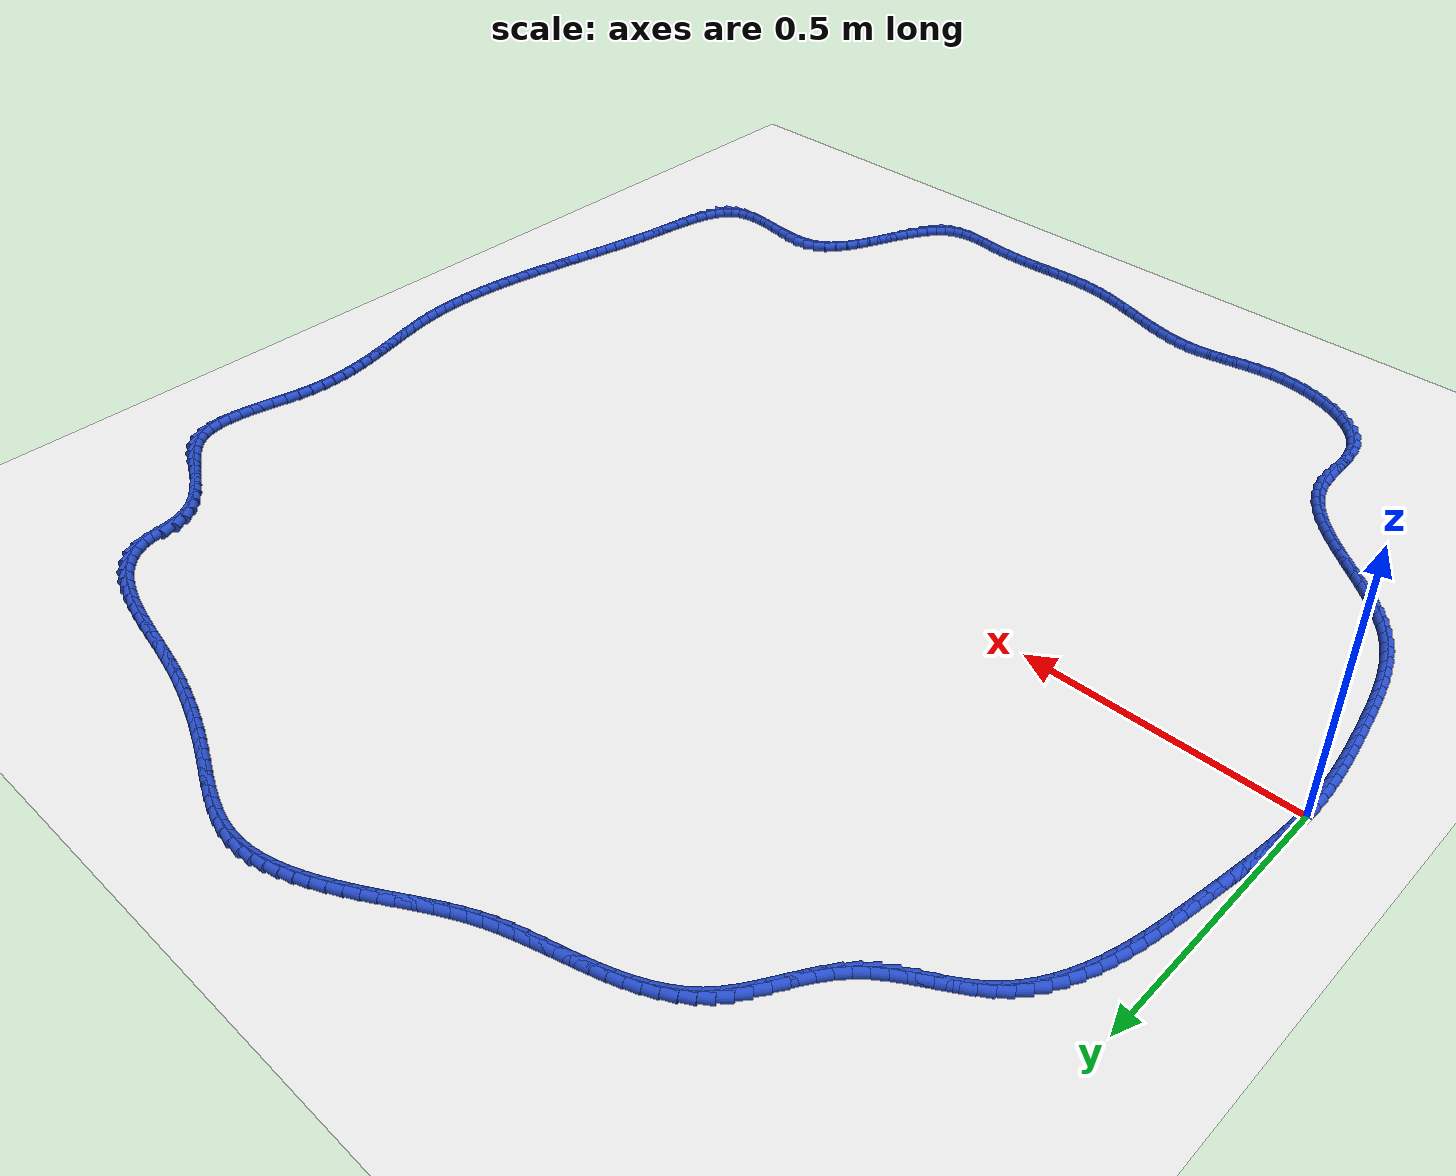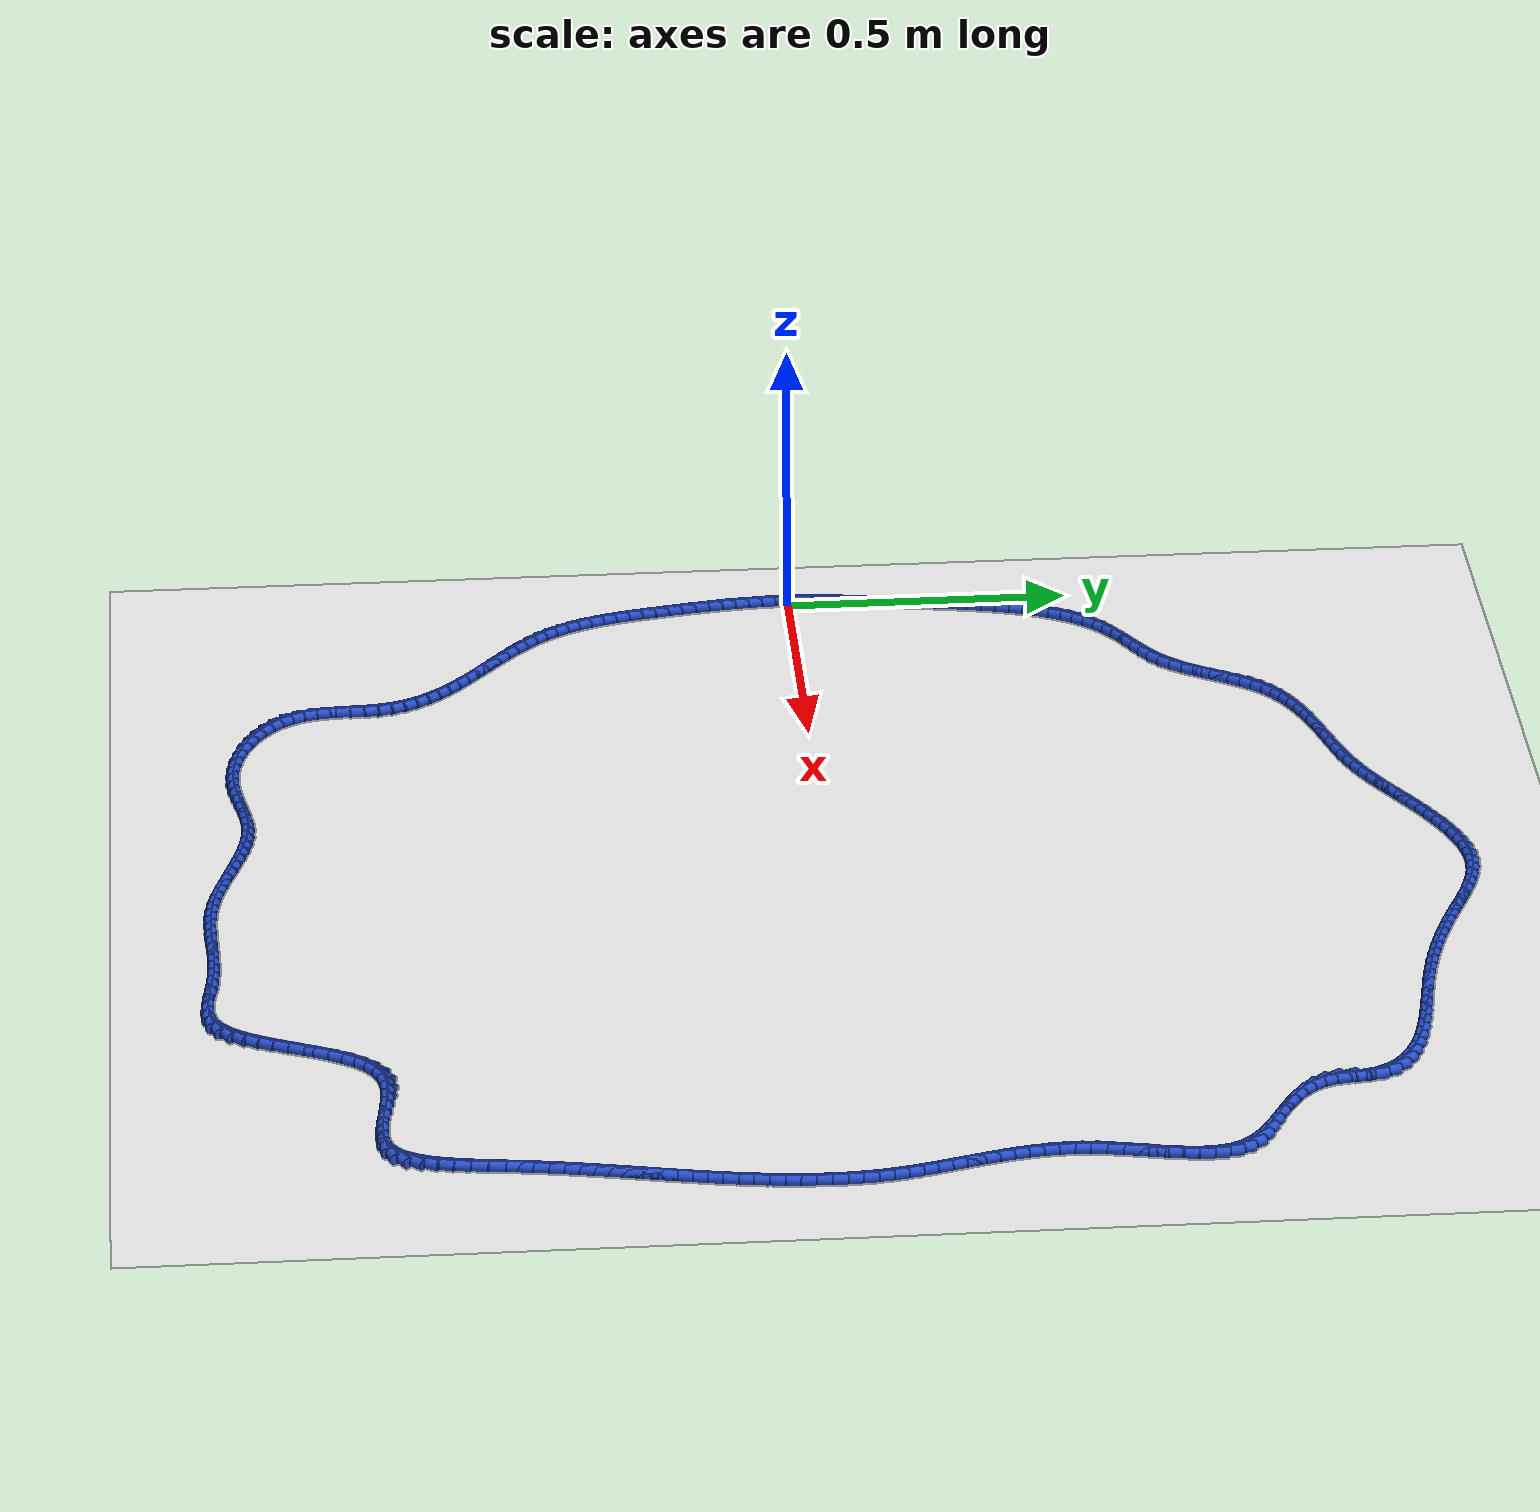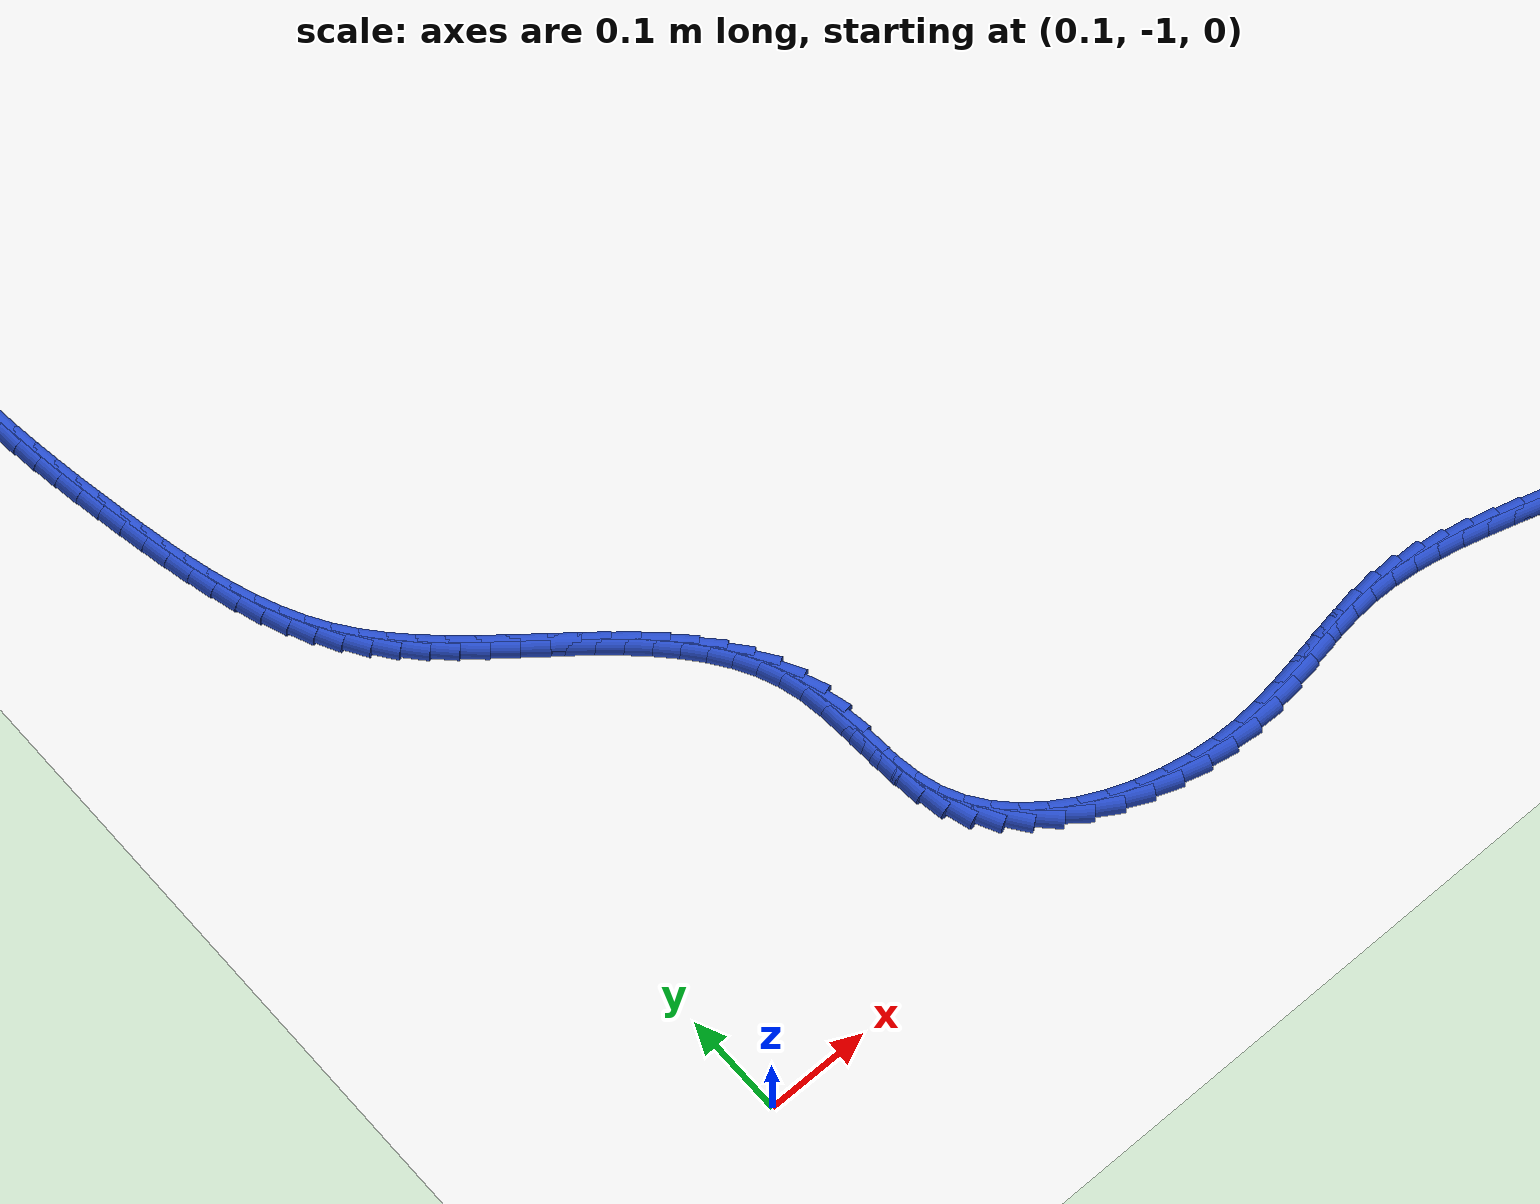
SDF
<sdf version="1.6">
 <world name="default">
  <light name="sun" type="directional">
   <pose>0 0 10 0 -0 0</pose>
   <diffuse>0.8 0.8 0.8 1</diffuse>
   <specular>0.2 0.2 0.2 1</specular>
   <attenuation>
    <range>1000</range>
    <constant>0.9</constant>
    <linear>0.01</linear>
    <quadratic>0.001</quadratic>
   </attenuation>
   <direction>-0.5 0.1 -0.9</direction>
  </light>
  <model name="ground_plane">
   <static>1</static>
   <link name="link">
    <collision name="collision">
     <geometry><plane><normal>0 0 1</normal><size>100 100</size></plane></geometry>
     <surface><friction><ode><mu>100</mu><mu2>50</mu2></ode></friction></surface>
    </collision>
    <visual name="visual">
     <cast_shadows>0</cast_shadows>
     <geometry><plane><normal>0 0 1</normal><size>100 100</size></plane></geometry>
     <material>
      <script><uri>file://media/materials/scripts/gazebo.material</uri><name>Gazebo/WhiteGlow</name></script>
     </material>
    </visual>
   </link>
  </model>
  <gravity>0 0 -9.8</gravity>
  <magnetic_field>6e-06 2.3e-05 -4.2e-05</magnetic_field>
  <atmosphere type="adiabatic"/>
  <physics name="default_physics" default="0" type="ode">
   <max_step_size>0.001</max_step_size>
   <real_time_factor>1</real_time_factor>
   <real_time_update_rate>1000</real_time_update_rate>
  </physics>
  <scene><ambient>0.4 0.4 0.4 1</ambient><background>0.7 0.7 0.7 1</background><shadows>1</shadows></scene>
  <spherical_coordinates>
   <surface_model>EARTH_WGS84</surface_model>
   <latitude_deg>0</latitude_deg>
   <longitude_deg>0</longitude_deg>
   <elevation>0</elevation>
   <heading_deg>0</heading_deg>
  </spherical_coordinates>
  <model name="line">
   <link name="link_0">
    <pose>-8.673617379884035e-18 4.163336342344337e-17 0.01 0 1.57 1.5476793691538977</pose>
    <collision name="collision">
     <geometry><cylinder><radius>0.01</radius><length>0.08</length></cylinder></geometry>
    </collision>
    <visual name="visual">
     <material>
      <script><name>Gazebo/Blue</name><uri>file://media/materials/scripts/gazebo.material</uri></script>
     </material>
     <geometry><cylinder><radius>0.01</radius><length>0.08</length></cylinder></geometry>
    </visual>
   </link>
   <link name="link_1">
    <pose>0.0005523613203440264 0.023889948349005933 0.01 0 1.57 1.5161205672506612</pose>
    <collision name="collision">
     <geometry><cylinder><radius>0.01</radius><length>0.08</length></cylinder></geometry>
    </collision>
    <visual name="visual">
     <material>
      <script><name>Gazebo/Blue</name><uri>file://media/materials/scripts/gazebo.material</uri></script>
     </material>
     <geometry><cylinder><radius>0.01</radius><length>0.08</length></cylinder></geometry>
    </visual>
   </link>
   <link name="link_2">
    <pose>0.0018581088642134508 0.04774779951772081 0.01 0 1.57 1.488601115384985</pose>
    <collision name="collision">
     <geometry><cylinder><radius>0.01</radius><length>0.08</length></cylinder></geometry>
    </collision>
    <visual name="visual">
     <material>
      <script><name>Gazebo/Blue</name><uri>file://media/materials/scripts/gazebo.material</uri></script>
     </material>
     <geometry><cylinder><radius>0.01</radius><length>0.08</length></cylinder></geometry>
    </visual>
   </link>
   <link name="link_3">
    <pose>0.0038248384821236332 0.0716214349568103 0.01 0 1.57 1.465275217036072</pose>
    <collision name="collision">
     <geometry><cylinder><radius>0.01</radius><length>0.08</length></cylinder></geometry>
    </collision>
    <visual name="visual">
     <material>
      <script><name>Gazebo/Blue</name><uri>file://media/materials/scripts/gazebo.material</uri></script>
     </material>
     <geometry><cylinder><radius>0.01</radius><length>0.08</length></cylinder></geometry>
    </visual>
   </link>
   <link name="link_4">
    <pose>0.006360146024589938 0.09555873611693988 0.01 0 1.57 1.446221262091227</pose>
    <collision name="collision">
     <geometry><cylinder><radius>0.01</radius><length>0.08</length></cylinder></geometry>
    </collision>
    <visual name="visual">
     <material>
      <script><name>Gazebo/Blue</name><uri>file://media/materials/scripts/gazebo.material</uri></script>
     </material>
     <geometry><cylinder><radius>0.01</radius><length>0.08</length></cylinder></geometry>
    </visual>
   </link>
   <link name="link_5">
    <pose>0.009371627342127748 0.11960758444877528 0.01 0 1.57 1.4314535750246575</pose>
    <collision name="collision">
     <geometry><cylinder><radius>0.01</radius><length>0.08</length></cylinder></geometry>
    </collision>
    <visual name="visual">
     <material>
      <script><name>Gazebo/Blue</name><uri>file://media/materials/scripts/gazebo.material</uri></script>
     </material>
     <geometry><cylinder><radius>0.01</radius><length>0.08</length></cylinder></geometry>
    </visual>
   </link>
   <link name="link_6">
    <pose>0.012766878285252423 0.14381586140298203 0.01 0 1.57 1.420934022808521</pose>
    <collision name="collision">
     <geometry><cylinder><radius>0.01</radius><length>0.08</length></cylinder></geometry>
    </collision>
    <visual name="visual">
     <material>
      <script><name>Gazebo/Blue</name><uri>file://media/materials/scripts/gazebo.material</uri></script>
     </material>
     <geometry><cylinder><radius>0.01</radius><length>0.08</length></cylinder></geometry>
    </visual>
   </link>
   <link name="link_7">
    <pose>0.016453494704479335 0.16823144843022567 0.01 0 1.57 1.4145823721288462</pose>
    <collision name="collision">
     <geometry><cylinder><radius>0.01</radius><length>0.08</length></cylinder></geometry>
    </collision>
    <visual name="visual">
     <material>
      <script><name>Gazebo/Blue</name><uri>file://media/materials/scripts/gazebo.material</uri></script>
     </material>
     <geometry><cylinder><radius>0.01</radius><length>0.08</length></cylinder></geometry>
    </visual>
   </link>
   <link name="link_8">
    <pose>0.020339072450323858 0.19290222698117188 0.01 0 1.57 1.4122847955080255</pose>
    <collision name="collision">
     <geometry><cylinder><radius>0.01</radius><length>0.08</length></cylinder></geometry>
    </collision>
    <visual name="visual">
     <material>
      <script><name>Gazebo/Blue</name><uri>file://media/materials/scripts/gazebo.material</uri></script>
     </material>
     <geometry><cylinder><radius>0.01</radius><length>0.08</length></cylinder></geometry>
    </visual>
   </link>
   <link name="link_9">
    <pose>0.024331207373301356 0.21787607850648616 0.01 0 1.57 1.4130104548541869</pose>
    <collision name="collision">
     <geometry><cylinder><radius>0.01</radius><length>0.08</length></cylinder></geometry>
    </collision>
    <visual name="visual">
     <material>
      <script><name>Gazebo/Blue</name><uri>file://media/materials/scripts/gazebo.material</uri></script>
     </material>
     <geometry><cylinder><radius>0.01</radius><length>0.08</length></cylinder></geometry>
    </visual>
   </link>
   <link name="link_10">
    <pose>0.02835785197488939 0.24318362134552063 0.01 0 1.57 1.4104538971865246</pose>
    <collision name="collision">
     <geometry><cylinder><radius>0.01</radius><length>0.08</length></cylinder></geometry>
    </collision>
    <visual name="visual">
     <material>
      <script><name>Gazebo/Blue</name><uri>file://media/materials/scripts/gazebo.material</uri></script>
     </material>
     <geometry><cylinder><radius>0.01</radius><length>0.08</length></cylinder></geometry>
    </visual>
   </link>
   <link name="link_11">
    <pose>0.032490143676954665 0.26873404830335434 0.01 0 1.57 1.4020292559087015</pose>
    <collision name="collision">
     <geometry><cylinder><radius>0.01</radius><length>0.08</length></cylinder></geometry>
    </collision>
    <visual name="visual">
     <material>
      <script><name>Gazebo/Blue</name><uri>file://media/materials/scripts/gazebo.material</uri></script>
     </material>
     <geometry><cylinder><radius>0.01</radius><length>0.08</length></cylinder></geometry>
    </visual>
   </link>
   <link name="link_12">
    <pose>0.03686065984181403 0.29438444908947103 0.01 0 1.57 1.387705604547025</pose>
    <collision name="collision">
     <geometry><cylinder><radius>0.01</radius><length>0.08</length></cylinder></geometry>
    </collision>
    <visual name="visual">
     <material>
      <script><name>Gazebo/Blue</name><uri>file://media/materials/scripts/gazebo.material</uri></script>
     </material>
     <geometry><cylinder><radius>0.01</radius><length>0.08</length></cylinder></geometry>
    </visual>
   </link>
   <link name="link_13">
    <pose>0.041602213613726735 0.3199917134624919 0.01 0 1.57 1.3673109148056917</pose>
    <collision name="collision">
     <geometry><cylinder><radius>0.01</radius><length>0.08</length></cylinder></geometry>
    </collision>
    <visual name="visual">
     <material>
      <script><name>Gazebo/Blue</name><uri>file://media/materials/scripts/gazebo.material</uri></script>
     </material>
     <geometry><cylinder><radius>0.01</radius><length>0.08</length></cylinder></geometry>
    </visual>
   </link>
   <link name="link_14">
    <pose>0.04684761813695201 0.34541273118103794 0.01 0 1.57 1.34053101223798</pose>
    <collision name="collision">
     <geometry><cylinder><radius>0.01</radius><length>0.08</length></cylinder></geometry>
    </collision>
    <visual name="visual">
     <material>
      <script><name>Gazebo/Blue</name><uri>file://media/materials/scripts/gazebo.material</uri></script>
     </material>
     <geometry><cylinder><radius>0.01</radius><length>0.08</length></cylinder></geometry>
    </visual>
   </link>
   <link name="link_15">
    <pose>0.05272968655574909 0.3705043920037303 0.01 0 1.57 1.3069193155320888</pose>
    <collision name="collision">
     <geometry><cylinder><radius>0.01</radius><length>0.08</length></cylinder></geometry>
    </collision>
    <visual name="visual">
     <material>
      <script><name>Gazebo/Blue</name><uri>file://media/materials/scripts/gazebo.material</uri></script>
     </material>
     <geometry><cylinder><radius>0.01</radius><length>0.08</length></cylinder></geometry>
    </visual>
   </link>
   <link name="link_16">
    <pose>0.05938123201437724 0.39512358568919054 0.01 0 1.57 1.2659123271466093</pose>
    <collision name="collision">
     <geometry><cylinder><radius>0.01</radius><length>0.08</length></cylinder></geometry>
    </collision>
    <visual name="visual">
     <material>
      <script><name>Gazebo/Blue</name><uri>file://media/materials/scripts/gazebo.material</uri></script>
     </material>
     <geometry><cylinder><radius>0.01</radius><length>0.08</length></cylinder></geometry>
    </visual>
   </link>
   <link name="link_17">
    <pose>0.06693506765709567 0.4191272019960395 0.01 0 1.57 1.2168586252389164</pose>
    <collision name="collision">
     <geometry><cylinder><radius>0.01</radius><length>0.08</length></cylinder></geometry>
    </collision>
    <visual name="visual">
     <material>
      <script><name>Gazebo/Blue</name><uri>file://media/materials/scripts/gazebo.material</uri></script>
     </material>
     <geometry><cylinder><radius>0.01</radius><length>0.08</length></cylinder></geometry>
    </visual>
   </link>
   <link name="link_18">
    <pose>0.07552400662816358 0.4423721306828983 0.01 0 1.57 1.1590722093257406</pose>
    <collision name="collision">
     <geometry><cylinder><radius>0.01</radius><length>0.08</length></cylinder></geometry>
    </collision>
    <visual name="visual">
     <material>
      <script><name>Gazebo/Blue</name><uri>file://media/materials/scripts/gazebo.material</uri></script>
     </material>
     <geometry><cylinder><radius>0.01</radius><length>0.08</length></cylinder></geometry>
    </visual>
   </link>
   <link name="link_19">
    <pose>0.08528086207184031 0.4647152615083884 0.01 0 1.57 1.0919236868609377</pose>
    <collision name="collision">
     <geometry><cylinder><radius>0.01</radius><length>0.08</length></cylinder></geometry>
    </collision>
    <visual name="visual">
     <material>
      <script><name>Gazebo/Blue</name><uri>file://media/materials/scripts/gazebo.material</uri></script>
     </material>
     <geometry><cylinder><radius>0.01</radius><length>0.08</length></cylinder></geometry>
    </visual>
   </link>
   <link name="link_20">
    <pose>0.09633844713238501 0.48601348423113067 0.01 0 1.57 1.0149820266887857</pose>
    <collision name="collision">
     <geometry><cylinder><radius>0.01</radius><length>0.08</length></cylinder></geometry>
    </collision>
    <visual name="visual">
     <material>
      <script><name>Gazebo/Blue</name><uri>file://media/materials/scripts/gazebo.material</uri></script>
     </material>
     <geometry><cylinder><radius>0.01</radius><length>0.08</length></cylinder></geometry>
    </visual>
   </link>
   <link name="link_21">
    <pose>0.10882957495405696 0.5061236886097465 0.01 0 1.57 0.9282099897694731</pose>
    <collision name="collision">
     <geometry><cylinder><radius>0.01</radius><length>0.08</length></cylinder></geometry>
    </collision>
    <visual name="visual">
     <material>
      <script><name>Gazebo/Blue</name><uri>file://media/materials/scripts/gazebo.material</uri></script>
     </material>
     <geometry><cylinder><radius>0.01</radius><length>0.08</length></cylinder></geometry>
    </visual>
   </link>
   <link name="link_22">
    <pose>0.12288705868111538 0.5249027644028571 0.01 0 1.57 0.8321913982158111</pose>
    <collision name="collision">
     <geometry><cylinder><radius>0.01</radius><length>0.08</length></cylinder></geometry>
    </collision>
    <visual name="visual">
     <material>
      <script><name>Gazebo/Blue</name><uri>file://media/materials/scripts/gazebo.material</uri></script>
     </material>
     <geometry><cylinder><radius>0.01</radius><length>0.08</length></cylinder></geometry>
    </visual>
   </link>
   <link name="link_23">
    <pose>0.13864371145781954 0.5422076013690835 0.01 0 1.57 0.72850812107362</pose>
    <collision name="collision">
     <geometry><cylinder><radius>0.01</radius><length>0.08</length></cylinder></geometry>
    </collision>
    <visual name="visual">
     <material>
      <script><name>Gazebo/Blue</name><uri>file://media/materials/scripts/gazebo.material</uri></script>
     </material>
     <geometry><cylinder><radius>0.01</radius><length>0.08</length></cylinder></geometry>
    </visual>
   </link>
   <link name="link_24">
    <pose>0.15622931838459708 0.5578980851390335 0.01 0 1.57 0.6333008512239515</pose>
    <collision name="collision">
     <geometry><cylinder><radius>0.01</radius><length>0.08</length></cylinder></geometry>
    </collision>
    <visual name="visual">
     <material>
      <script><name>Gazebo/Blue</name><uri>file://media/materials/scripts/gazebo.material</uri></script>
     </material>
     <geometry><cylinder><radius>0.01</radius><length>0.08</length></cylinder></geometry>
    </visual>
   </link>
   <link name="link_25">
    <pose>0.17553398487890415 0.5720712345183899 0.01 0 1.57 0.5705224568081297</pose>
    <collision name="collision">
     <geometry><cylinder><radius>0.01</radius><length>0.08</length></cylinder></geometry>
    </collision>
    <visual name="visual">
     <material>
      <script><name>Gazebo/Blue</name><uri>file://media/materials/scripts/gazebo.material</uri></script>
     </material>
     <geometry><cylinder><radius>0.01</radius><length>0.08</length></cylinder></geometry>
    </visual>
   </link>
   <link name="link_26">
    <pose>0.19603845889019939 0.5852290765092869 0.01 0 1.57 0.5403216537165627</pose>
    <collision name="collision">
     <geometry><cylinder><radius>0.01</radius><length>0.08</length></cylinder></geometry>
    </collision>
    <visual name="visual">
     <material>
      <script><name>Gazebo/Blue</name><uri>file://media/materials/scripts/gazebo.material</uri></script>
     </material>
     <geometry><cylinder><radius>0.01</radius><length>0.08</length></cylinder></geometry>
    </visual>
   </link>
   <link name="link_27">
    <pose>0.2171834459353987 0.5979132551103803 0.01 0 1.57 0.5409886579165198</pose>
    <collision name="collision">
     <geometry><cylinder><radius>0.01</radius><length>0.08</length></cylinder></geometry>
    </collision>
    <visual name="visual">
     <material>
      <script><name>Gazebo/Blue</name><uri>file://media/materials/scripts/gazebo.material</uri></script>
     </material>
     <geometry><cylinder><radius>0.01</radius><length>0.08</length></cylinder></geometry>
    </visual>
   </link>
   <link name="link_28">
    <pose>0.23840965153141822 0.6106654143203258 0.01 0 1.57 0.5721453256293433</pose>
    <collision name="collision">
     <geometry><cylinder><radius>0.01</radius><length>0.08</length></cylinder></geometry>
    </collision>
    <visual name="visual">
     <material>
      <script><name>Gazebo/Blue</name><uri>file://media/materials/scripts/gazebo.material</uri></script>
     </material>
     <geometry><cylinder><radius>0.01</radius><length>0.08</length></cylinder></geometry>
    </visual>
   </link>
   <link name="link_29">
    <pose>0.25915778119517385 0.6240271981377796 0.01 0 1.57 0.6346759686867859</pose>
    <collision name="collision">
     <geometry><cylinder><radius>0.01</radius><length>0.08</length></cylinder></geometry>
    </collision>
    <visual name="visual">
     <material>
      <script><name>Gazebo/Blue</name><uri>file://media/materials/scripts/gazebo.material</uri></script>
     </material>
     <geometry><cylinder><radius>0.01</radius><length>0.08</length></cylinder></geometry>
    </visual>
   </link>
   <link name="link_30">
    <pose>0.2788685404435815 0.6385402505613973 0.01 0 1.57 0.7298463462555387</pose>
    <collision name="collision">
     <geometry><cylinder><radius>0.01</radius><length>0.08</length></cylinder></geometry>
    </collision>
    <visual name="visual">
     <material>
      <script><name>Gazebo/Blue</name><uri>file://media/materials/scripts/gazebo.material</uri></script>
     </material>
     <geometry><cylinder><radius>0.01</radius><length>0.08</length></cylinder></geometry>
    </visual>
   </link>
   <link name="link_31">
    <pose>0.2969828186777341 0.6547460239418198 0.01 0 1.57 0.8434917342189491</pose>
    <collision name="collision">
     <geometry><cylinder><radius>0.01</radius><length>0.08</length></cylinder></geometry>
    </collision>
    <visual name="visual">
     <material>
      <script><name>Gazebo/Blue</name><uri>file://media/materials/scripts/gazebo.material</uri></script>
     </material>
     <geometry><cylinder><radius>0.01</radius><length>0.08</length></cylinder></geometry>
    </visual>
   </link>
   <link name="link_32">
    <pose>0.31317715467941326 0.6729403718139563 0.01 0 1.57 0.9326730001134195</pose>
    <collision name="collision">
     <geometry><cylinder><radius>0.01</radius><length>0.08</length></cylinder></geometry>
    </collision>
    <visual name="visual">
     <material>
      <script><name>Gazebo/Blue</name><uri>file://media/materials/scripts/gazebo.material</uri></script>
     </material>
     <geometry><cylinder><radius>0.01</radius><length>0.08</length></cylinder></geometry>
    </visual>
   </link>
   <link name="link_33">
    <pose>0.32782566175312094 0.6926921206517328 0.01 0 1.57 0.9903112232157183</pose>
    <collision name="collision">
     <geometry><cylinder><radius>0.01</radius><length>0.08</length></cylinder></geometry>
    </collision>
    <visual name="visual">
     <material>
      <script><name>Gazebo/Blue</name><uri>file://media/materials/scripts/gazebo.material</uri></script>
     </material>
     <geometry><cylinder><radius>0.01</radius><length>0.08</length></cylinder></geometry>
    </visual>
   </link>
   <link name="link_34">
    <pose>0.3414309194935599 0.7134362066186392 0.01 0 1.57 1.0179069093631676</pose>
    <collision name="collision">
     <geometry><cylinder><radius>0.01</radius><length>0.08</length></cylinder></geometry>
    </collision>
    <visual name="visual">
     <material>
      <script><name>Gazebo/Blue</name><uri>file://media/materials/scripts/gazebo.material</uri></script>
     </material>
     <geometry><cylinder><radius>0.01</radius><length>0.08</length></cylinder></geometry>
    </visual>
   </link>
   <link name="link_35">
    <pose>0.35449550749543235 0.7346075658781642 0.01 0 1.57 1.0162923461349398</pose>
    <collision name="collision">
     <geometry><cylinder><radius>0.01</radius><length>0.08</length></cylinder></geometry>
    </collision>
    <visual name="visual">
     <material>
      <script><name>Gazebo/Blue</name><uri>file://media/materials/scripts/gazebo.material</uri></script>
     </material>
     <geometry><cylinder><radius>0.01</radius><length>0.08</length></cylinder></geometry>
    </visual>
   </link>
   <link name="link_36">
    <pose>0.36752200535344104 0.7556411345937978 0.01 0 1.57 0.9849360176026919</pose>
    <collision name="collision">
     <geometry><cylinder><radius>0.01</radius><length>0.08</length></cylinder></geometry>
    </collision>
    <visual name="visual">
     <material>
      <script><name>Gazebo/Blue</name><uri>file://media/materials/scripts/gazebo.material</uri></script>
     </material>
     <geometry><cylinder><radius>0.01</radius><length>0.08</length></cylinder></geometry>
    </visual>
   </link>
   <link name="link_37">
    <pose>0.3810129926622886 0.7759718489290295 0.01 0 1.57 0.921913157869965</pose>
    <collision name="collision">
     <geometry><cylinder><radius>0.01</radius><length>0.08</length></cylinder></geometry>
    </collision>
    <visual name="visual">
     <material>
      <script><name>Gazebo/Blue</name><uri>file://media/materials/scripts/gazebo.material</uri></script>
     </material>
     <geometry><cylinder><radius>0.01</radius><length>0.08</length></cylinder></geometry>
    </visual>
   </link>
   <link name="link_38">
    <pose>0.39547104901667735 0.7950346450473482 0.01 0 1.57 0.8248569017872066</pose>
    <collision name="collision">
     <geometry><cylinder><radius>0.01</radius><length>0.08</length></cylinder></geometry>
    </collision>
    <visual name="visual">
     <material>
      <script><name>Gazebo/Blue</name><uri>file://media/materials/scripts/gazebo.material</uri></script>
     </material>
     <geometry><cylinder><radius>0.01</radius><length>0.08</length></cylinder></geometry>
    </visual>
   </link>
   <link name="link_39">
    <pose>0.41139553875256607 0.8122681884023746 0.01 0 1.57 0.7086927014092843</pose>
    <collision name="collision">
     <geometry><cylinder><radius>0.01</radius><length>0.08</length></cylinder></geometry>
    </collision>
    <visual name="visual">
     <material>
      <script><name>Gazebo/Blue</name><uri>file://media/materials/scripts/gazebo.material</uri></script>
     </material>
     <geometry><cylinder><radius>0.01</radius><length>0.08</length></cylinder></geometry>
    </visual>
   </link>
   <link name="link_40">
    <pose>0.4290411034506362 0.8273949916366288 0.01 0 1.57 0.6028204289810302</pose>
    <collision name="collision">
     <geometry><cylinder><radius>0.01</radius><length>0.08</length></cylinder></geometry>
    </collision>
    <visual name="visual">
     <material>
      <script><name>Gazebo/Blue</name><uri>file://media/materials/scripts/gazebo.material</uri></script>
     </material>
     <geometry><cylinder><radius>0.01</radius><length>0.08</length></cylinder></geometry>
    </visual>
   </link>
   <link name="link_41">
    <pose>0.44824983096740956 0.8406160771035082 0.01 0 1.57 0.5119968472825748</pose>
    <collision name="collision">
     <geometry><cylinder><radius>0.01</radius><length>0.08</length></cylinder></geometry>
    </collision>
    <visual name="visual">
     <material>
      <script><name>Gazebo/Blue</name><uri>file://media/materials/scripts/gazebo.material</uri></script>
     </material>
     <geometry><cylinder><radius>0.01</radius><length>0.08</length></cylinder></geometry>
    </visual>
   </link>
   <link name="link_42">
    <pose>0.46882413049327404 0.8521784893492739 0.01 0 1.57 0.43679279473904</pose>
    <collision name="collision">
     <geometry><cylinder><radius>0.01</radius><length>0.08</length></cylinder></geometry>
    </collision>
    <visual name="visual">
     <material>
      <script><name>Gazebo/Blue</name><uri>file://media/materials/scripts/gazebo.material</uri></script>
     </material>
     <geometry><cylinder><radius>0.01</radius><length>0.08</length></cylinder></geometry>
    </visual>
   </link>
   <link name="link_43">
    <pose>0.4905664112186179 0.8623292729201868 0.01 0 1.57 0.3767481389557139</pose>
    <collision name="collision">
     <geometry><cylinder><radius>0.01</radius><length>0.08</length></cylinder></geometry>
    </collision>
    <visual name="visual">
     <material>
      <script><name>Gazebo/Blue</name><uri>file://media/materials/scripts/gazebo.material</uri></script>
     </material>
     <geometry><cylinder><radius>0.01</radius><length>0.08</length></cylinder></geometry>
    </visual>
   </link>
   <link name="link_44">
    <pose>0.5132790823338294 0.8713154723625084 0.01 0 1.57 0.3309258234886349</pose>
    <collision name="collision">
     <geometry><cylinder><radius>0.01</radius><length>0.08</length></cylinder></geometry>
    </collision>
    <visual name="visual">
     <material>
      <script><name>Gazebo/Blue</name><uri>file://media/materials/scripts/gazebo.material</uri></script>
     </material>
     <geometry><cylinder><radius>0.01</radius><length>0.08</length></cylinder></geometry>
    </visual>
   </link>
   <link name="link_45">
    <pose>0.5367645530292958 0.8793841322224989 0.01 0 1.57 0.2983044842982421</pose>
    <collision name="collision">
     <geometry><cylinder><radius>0.01</radius><length>0.08</length></cylinder></geometry>
    </collision>
    <visual name="visual">
     <material>
      <script><name>Gazebo/Blue</name><uri>file://media/materials/scripts/gazebo.material</uri></script>
     </material>
     <geometry><cylinder><radius>0.01</radius><length>0.08</length></cylinder></geometry>
    </visual>
   </link>
   <link name="link_46">
    <pose>0.5608252324954058 0.8867822970464199 0.01 0 1.57 0.2780099863476112</pose>
    <collision name="collision">
     <geometry><cylinder><radius>0.01</radius><length>0.08</length></cylinder></geometry>
    </collision>
    <visual name="visual">
     <material>
      <script><name>Gazebo/Blue</name><uri>file://media/materials/scripts/gazebo.material</uri></script>
     </material>
     <geometry><cylinder><radius>0.01</radius><length>0.08</length></cylinder></geometry>
    </visual>
   </link>
   <link name="link_47">
    <pose>0.5852635299225472 0.8937570113805323 0.01 0 1.57 0.269433459123871</pose>
    <collision name="collision">
     <geometry><cylinder><radius>0.01</radius><length>0.08</length></cylinder></geometry>
    </collision>
    <visual name="visual">
     <material>
      <script><name>Gazebo/Blue</name><uri>file://media/materials/scripts/gazebo.material</uri></script>
     </material>
     <geometry><cylinder><radius>0.01</radius><length>0.08</length></cylinder></geometry>
    </visual>
   </link>
   <link name="link_48">
    <pose>0.609881854501108 0.9005553197710969 0.01 0 1.57 0.27228234156356423</pose>
    <collision name="collision">
     <geometry><cylinder><radius>0.01</radius><length>0.08</length></cylinder></geometry>
    </collision>
    <visual name="visual">
     <material>
      <script><name>Gazebo/Blue</name><uri>file://media/materials/scripts/gazebo.material</uri></script>
     </material>
     <geometry><cylinder><radius>0.01</radius><length>0.08</length></cylinder></geometry>
    </visual>
   </link>
   <link name="link_49">
    <pose>0.6344826154214761 0.9074242667643749 0.01 0 1.57 0.28659458577741215</pose>
    <collision name="collision">
     <geometry><cylinder><radius>0.01</radius><length>0.08</length></cylinder></geometry>
    </collision>
    <visual name="visual">
     <material>
      <script><name>Gazebo/Blue</name><uri>file://media/materials/scripts/gazebo.material</uri></script>
     </material>
     <geometry><cylinder><radius>0.01</radius><length>0.08</length></cylinder></geometry>
    </visual>
   </link>
   <link name="link_50">
    <pose>0.6588682218740398 0.9146108969066272 0.01 0 1.57 0.3127287307479492</pose>
    <collision name="collision">
     <geometry><cylinder><radius>0.01</radius><length>0.08</length></cylinder></geometry>
    </collision>
    <visual name="visual">
     <material>
      <script><name>Gazebo/Blue</name><uri>file://media/materials/scripts/gazebo.material</uri></script>
     </material>
     <geometry><cylinder><radius>0.01</radius><length>0.08</length></cylinder></geometry>
    </visual>
   </link>
   <link name="link_51">
    <pose>0.6828410830491869 0.9223622547441148 0.01 0 1.57 0.3513267244276863</pose>
    <collision name="collision">
     <geometry><cylinder><radius>0.01</radius><length>0.08</length></cylinder></geometry>
    </collision>
    <visual name="visual">
     <material>
      <script><name>Gazebo/Blue</name><uri>file://media/materials/scripts/gazebo.material</uri></script>
     </material>
     <geometry><cylinder><radius>0.01</radius><length>0.08</length></cylinder></geometry>
    </visual>
   </link>
   <link name="link_52">
    <pose>0.7062036081373054 0.9309253848230987 0.01 0 1.57 0.4003787179667804</pose>
    <collision name="collision">
     <geometry><cylinder><radius>0.01</radius><length>0.08</length></cylinder></geometry>
    </collision>
    <visual name="visual">
     <material>
      <script><name>Gazebo/Blue</name><uri>file://media/materials/scripts/gazebo.material</uri></script>
     </material>
     <geometry><cylinder><radius>0.01</radius><length>0.08</length></cylinder></geometry>
    </visual>
   </link>
   <link name="link_53">
    <pose>0.7288064571793971 0.9404918079975982 0.01 0 1.57 0.44558805196662177</pose>
    <collision name="collision">
     <geometry><cylinder><radius>0.01</radius><length>0.08</length></cylinder></geometry>
    </collision>
    <visual name="visual">
     <material>
      <script><name>Gazebo/Blue</name><uri>file://media/materials/scripts/gazebo.material</uri></script>
     </material>
     <geometry><cylinder><radius>0.01</radius><length>0.08</length></cylinder></geometry>
    </visual>
   </link>
   <link name="link_54">
    <pose>0.7507457628767894 0.9509705724134323 0.01 0 1.57 0.4815967942809413</pose>
    <collision name="collision">
     <geometry><cylinder><radius>0.01</radius><length>0.08</length></cylinder></geometry>
    </collision>
    <visual name="visual">
     <material>
      <script><name>Gazebo/Blue</name><uri>file://media/materials/scripts/gazebo.material</uri></script>
     </material>
     <geometry><cylinder><radius>0.01</radius><length>0.08</length></cylinder></geometry>
    </visual>
   </link>
   <link name="link_55">
    <pose>0.7721955254542361 0.9621811217358501 0.01 0 1.57 0.5078390887550811</pose>
    <collision name="collision">
     <geometry><cylinder><radius>0.01</radius><length>0.08</length></cylinder></geometry>
    </collision>
    <visual name="visual">
     <material>
      <script><name>Gazebo/Blue</name><uri>file://media/materials/scripts/gazebo.material</uri></script>
     </material>
     <geometry><cylinder><radius>0.01</radius><length>0.08</length></cylinder></geometry>
    </visual>
   </link>
   <link name="link_56">
    <pose>0.7933297766884574 0.9739428633223114 0.01 0 1.57 0.5240330602664679</pose>
    <collision name="collision">
     <geometry><cylinder><radius>0.01</radius><length>0.08</length></cylinder></geometry>
    </collision>
    <visual name="visual">
     <material>
      <script><name>Gazebo/Blue</name><uri>file://media/materials/scripts/gazebo.material</uri></script>
     </material>
     <geometry><cylinder><radius>0.01</radius><length>0.08</length></cylinder></geometry>
    </visual>
   </link>
   <link name="link_57">
    <pose>0.8143225483561737 0.9860752045302761 0.01 0 1.57 0.5301151782161062</pose>
    <collision name="collision">
     <geometry><cylinder><radius>0.01</radius><length>0.08</length></cylinder></geometry>
    </collision>
    <visual name="visual">
     <material>
      <script><name>Gazebo/Blue</name><uri>file://media/materials/scripts/gazebo.material</uri></script>
     </material>
     <geometry><cylinder><radius>0.01</radius><length>0.08</length></cylinder></geometry>
    </visual>
   </link>
   <link name="link_58">
    <pose>0.8353478722341046 0.9983975527172034 0.01 0 1.57 0.5261917331973283</pose>
    <collision name="collision">
     <geometry><cylinder><radius>0.01</radius><length>0.08</length></cylinder></geometry>
    </collision>
    <visual name="visual">
     <material>
      <script><name>Gazebo/Blue</name><uri>file://media/materials/scripts/gazebo.material</uri></script>
     </material>
     <geometry><cylinder><radius>0.01</radius><length>0.08</length></cylinder></geometry>
    </visual>
   </link>
   <link name="link_59">
    <pose>0.8565797800989711 1.010729315240554 0.01 0 1.57 0.5125138652786664</pose>
    <collision name="collision">
     <geometry><cylinder><radius>0.01</radius><length>0.08</length></cylinder></geometry>
    </collision>
    <visual name="visual">
     <material>
      <script><name>Gazebo/Blue</name><uri>file://media/materials/scripts/gazebo.material</uri></script>
     </material>
     <geometry><cylinder><radius>0.01</radius><length>0.08</length></cylinder></geometry>
    </visual>
   </link>
   <link name="link_60">
    <pose>0.8781923037274931 1.0228898994577877 0.01 0 1.57 0.48969918213205776</pose>
    <collision name="collision">
     <geometry><cylinder><radius>0.01</radius><length>0.08</length></cylinder></geometry>
    </collision>
    <visual name="visual">
     <material>
      <script><name>Gazebo/Blue</name><uri>file://media/materials/scripts/gazebo.material</uri></script>
     </material>
     <geometry><cylinder><radius>0.01</radius><length>0.08</length></cylinder></geometry>
    </visual>
   </link>
   <link name="link_61">
    <pose>0.9003234439649656 1.0346858371994585 0.01 0 1.57 0.4589648728051434</pose>
    <collision name="collision">
     <geometry><cylinder><radius>0.01</radius><length>0.08</length></cylinder></geometry>
    </collision>
    <visual name="visual">
     <material>
      <script><name>Gazebo/Blue</name><uri>file://media/materials/scripts/gazebo.material</uri></script>
     </material>
     <geometry><cylinder><radius>0.01</radius><length>0.08</length></cylinder></geometry>
    </visual>
   </link>
   <link name="link_62">
    <pose>0.922943235800327 1.0458636382867763 0.01 0 1.57 0.4201564963937826</pose>
    <collision name="collision">
     <geometry><cylinder><radius>0.01</radius><length>0.08</length></cylinder></geometry>
    </collision>
    <visual name="visual">
     <material>
      <script><name>Gazebo/Blue</name><uri>file://media/materials/scripts/gazebo.material</uri></script>
     </material>
     <geometry><cylinder><radius>0.01</radius><length>0.08</length></cylinder></geometry>
    </visual>
   </link>
   <link name="link_63">
    <pose>0.9459728079881635 1.056152336069727 0.01 0 1.57 0.37252620290458976</pose>
    <collision name="collision">
     <geometry><cylinder><radius>0.01</radius><length>0.08</length></cylinder></geometry>
    </collision>
    <visual name="visual">
     <material>
      <script><name>Gazebo/Blue</name><uri>file://media/materials/scripts/gazebo.material</uri></script>
     </material>
     <geometry><cylinder><radius>0.01</radius><length>0.08</length></cylinder></geometry>
    </visual>
   </link>
   <link name="link_64">
    <pose>0.9693332837070703 1.065280961905734 0.01 0 1.57 0.31513263259168844</pose>
    <collision name="collision">
     <geometry><cylinder><radius>0.01</radius><length>0.08</length></cylinder></geometry>
    </collision>
    <visual name="visual">
     <material>
      <script><name>Gazebo/Blue</name><uri>file://media/materials/scripts/gazebo.material</uri></script>
     </material>
     <geometry><cylinder><radius>0.01</radius><length>0.08</length></cylinder></geometry>
    </visual>
   </link>
   <link name="link_65">
    <pose>0.9929457861356441 1.0729785471522226 0.01 0 1.57 0.24692304736091622</pose>
    <collision name="collision">
     <geometry><cylinder><radius>0.01</radius><length>0.08</length></cylinder></geometry>
    </collision>
    <visual name="visual">
     <material>
      <script><name>Gazebo/Blue</name><uri>file://media/materials/scripts/gazebo.material</uri></script>
     </material>
     <geometry><cylinder><radius>0.01</radius><length>0.08</length></cylinder></geometry>
    </visual>
   </link>
   <link name="link_66">
    <pose>1.016731438452481 1.0789741231666181 0.01 0 1.57 0.16688431533418271</pose>
    <collision name="collision">
     <geometry><cylinder><radius>0.01</radius><length>0.08</length></cylinder></geometry>
    </collision>
    <visual name="visual">
     <material>
      <script><name>Gazebo/Blue</name><uri>file://media/materials/scripts/gazebo.material</uri></script>
     </material>
     <geometry><cylinder><radius>0.01</radius><length>0.08</length></cylinder></geometry>
    </visual>
   </link>
   <link name="link_67">
    <pose>1.0406113638361767 1.0829967213063445 0.01 0 1.57 0.07429812415650835</pose>
    <collision name="collision">
     <geometry><cylinder><radius>0.01</radius><length>0.08</length></cylinder></geometry>
    </collision>
    <visual name="visual">
     <material>
      <script><name>Gazebo/Blue</name><uri>file://media/materials/scripts/gazebo.material</uri></script>
     </material>
     <geometry><cylinder><radius>0.01</radius><length>0.08</length></cylinder></geometry>
    </visual>
   </link>
   <link name="link_68">
    <pose>1.064506685465328 1.0847753729288272 0.01 0 1.57 -0.030781604601792342</pose>
    <collision name="collision">
     <geometry><cylinder><radius>0.01</radius><length>0.08</length></cylinder></geometry>
    </collision>
    <visual name="visual">
     <material>
      <script><name>Gazebo/Blue</name><uri>file://media/materials/scripts/gazebo.material</uri></script>
     </material>
     <geometry><cylinder><radius>0.01</radius><length>0.08</length></cylinder></geometry>
    </visual>
   </link>
   <link name="link_69">
    <pose>1.088338739323353 1.084041552288704 0.01 0 1.57 -0.13768963541557416</pose>
    <collision name="collision">
     <geometry><cylinder><radius>0.01</radius><length>0.08</length></cylinder></geometry>
    </collision>
    <visual name="visual">
     <material>
      <script><name>Gazebo/Blue</name><uri>file://media/materials/scripts/gazebo.material</uri></script>
     </material>
     <geometry><cylinder><radius>0.01</radius><length>0.08</length></cylinder></geometry>
    </visual>
   </link>
   <link name="link_70">
    <pose>1.1120488443266565 1.0807561281188243 0.01 0 1.57 -0.2277750487837812</pose>
    <collision name="collision">
     <geometry><cylinder><radius>0.01</radius><length>0.08</length></cylinder></geometry>
    </collision>
    <visual name="visual">
     <material>
      <script><name>Gazebo/Blue</name><uri>file://media/materials/scripts/gazebo.material</uri></script>
     </material>
     <geometry><cylinder><radius>0.01</radius><length>0.08</length></cylinder></geometry>
    </visual>
   </link>
   <link name="link_71">
    <pose>1.1356143599075235 1.0752936969737374 0.01 0 1.57 -0.2993117270301868</pose>
    <collision name="collision">
     <geometry><cylinder><radius>0.01</radius><length>0.08</length></cylinder></geometry>
    </collision>
    <visual name="visual">
     <material>
      <script><name>Gazebo/Blue</name><uri>file://media/materials/scripts/gazebo.material</uri></script>
     </material>
     <geometry><cylinder><radius>0.01</radius><length>0.08</length></cylinder></geometry>
    </visual>
   </link>
   <link name="link_72">
    <pose>1.1590164243356156 1.068072234647105 0.01 0 1.57 -0.3532888749653126</pose>
    <collision name="collision">
     <geometry><cylinder><radius>0.01</radius><length>0.08</length></cylinder></geometry>
    </collision>
    <visual name="visual">
     <material>
      <script><name>Gazebo/Blue</name><uri>file://media/materials/scripts/gazebo.material</uri></script>
     </material>
     <geometry><cylinder><radius>0.01</radius><length>0.08</length></cylinder></geometry>
    </visual>
   </link>
   <link name="link_73">
    <pose>1.1822361758805942 1.0595097169325876 0.01 0 1.57 -0.3908803922394566</pose>
    <collision name="collision">
     <geometry><cylinder><radius>0.01</radius><length>0.08</length></cylinder></geometry>
    </collision>
    <visual name="visual">
     <material>
      <script><name>Gazebo/Blue</name><uri>file://media/materials/scripts/gazebo.material</uri></script>
     </material>
     <geometry><cylinder><radius>0.01</radius><length>0.08</length></cylinder></geometry>
    </visual>
   </link>
   <link name="link_74">
    <pose>1.2052547528121202 1.0500241196238471 0.01 0 1.57 -0.41301183716383916</pose>
    <collision name="collision">
     <geometry><cylinder><radius>0.01</radius><length>0.08</length></cylinder></geometry>
    </collision>
    <visual name="visual">
     <material>
      <script><name>Gazebo/Blue</name><uri>file://media/materials/scripts/gazebo.material</uri></script>
     </material>
     <geometry><cylinder><radius>0.01</radius><length>0.08</length></cylinder></geometry>
    </visual>
   </link>
   <link name="link_75">
    <pose>1.2280532933998558 1.040033418514545 0.01 0 1.57 -0.42012239838867854</pose>
    <collision name="collision">
     <geometry><cylinder><radius>0.01</radius><length>0.08</length></cylinder></geometry>
    </collision>
    <visual name="visual">
     <material>
      <script><name>Gazebo/Blue</name><uri>file://media/materials/scripts/gazebo.material</uri></script>
     </material>
     <geometry><cylinder><radius>0.01</radius><length>0.08</length></cylinder></geometry>
    </visual>
   </link>
   <link name="link_76">
    <pose>1.2506129359134626 1.0299555893983423 0.01 0 1.57 -0.4122048784294975</pose>
    <collision name="collision">
     <geometry><cylinder><radius>0.01</radius><length>0.08</length></cylinder></geometry>
    </collision>
    <visual name="visual">
     <material>
      <script><name>Gazebo/Blue</name><uri>file://media/materials/scripts/gazebo.material</uri></script>
     </material>
     <geometry><cylinder><radius>0.01</radius><length>0.08</length></cylinder></geometry>
    </visual>
   </link>
   <link name="link_77">
    <pose>1.2729168796891315 1.0202030759473355 0.01 0 1.57 -0.3946114586932929</pose>
    <collision name="collision">
     <geometry><cylinder><radius>0.01</radius><length>0.08</length></cylinder></geometry>
    </collision>
    <visual name="visual">
     <material>
      <script><name>Gazebo/Blue</name><uri>file://media/materials/scripts/gazebo.material</uri></script>
     </material>
     <geometry><cylinder><radius>0.01</radius><length>0.08</length></cylinder></geometry>
    </visual>
   </link>
   <link name="link_78">
    <pose>1.2950190445514649 1.0109985005282993 0.01 0 1.57 -0.3746449762705941</pose>
    <collision name="collision">
     <geometry><cylinder><radius>0.01</radius><length>0.08</length></cylinder></geometry>
    </collision>
    <visual name="visual">
     <material>
      <script><name>Gazebo/Blue</name><uri>file://media/materials/scripts/gazebo.material</uri></script>
     </material>
     <geometry><cylinder><radius>0.01</radius><length>0.08</length></cylinder></geometry>
    </visual>
   </link>
   <link name="link_79">
    <pose>1.3170601211926019 1.0023315832796775 0.01 0 1.57 -0.35307470863193147</pose>
    <collision name="collision">
     <geometry><cylinder><radius>0.01</radius><length>0.08</length></cylinder></geometry>
    </collision>
    <visual name="visual">
     <material>
      <script><name>Gazebo/Blue</name><uri>file://media/materials/scripts/gazebo.material</uri></script>
     </material>
     <geometry><cylinder><radius>0.01</radius><length>0.08</length></cylinder></geometry>
    </visual>
   </link>
   <link name="link_80">
    <pose>1.339186113603525 0.9941777828812565 0.01 0 1.57 -0.33029726830299727</pose>
    <collision name="collision">
     <geometry><cylinder><radius>0.01</radius><length>0.08</length></cylinder></geometry>
    </collision>
    <visual name="visual">
     <material>
      <script><name>Gazebo/Blue</name><uri>file://media/materials/scripts/gazebo.material</uri></script>
     </material>
     <geometry><cylinder><radius>0.01</radius><length>0.08</length></cylinder></geometry>
    </visual>
   </link>
   <link name="link_81">
    <pose>1.361543025775215 0.9865125580128203 0.01 0 1.57 -0.3067619753542057</pose>
    <collision name="collision">
     <geometry><cylinder><radius>0.01</radius><length>0.08</length></cylinder></geometry>
    </collision>
    <visual name="visual">
     <material>
      <script><name>Gazebo/Blue</name><uri>file://media/materials/scripts/gazebo.material</uri></script>
     </material>
     <geometry><cylinder><radius>0.01</radius><length>0.08</length></cylinder></geometry>
    </visual>
   </link>
   <link name="link_82">
    <pose>1.384276861698654 0.9793113673541546 0.01 0 1.57 -0.2829409233831717</pose>
    <collision name="collision">
     <geometry><cylinder><radius>0.01</radius><length>0.08</length></cylinder></geometry>
    </collision>
    <visual name="visual">
     <material>
      <script><name>Gazebo/Blue</name><uri>file://media/materials/scripts/gazebo.material</uri></script>
     </material>
     <geometry><cylinder><radius>0.01</radius><length>0.08</length></cylinder></geometry>
    </visual>
   </link>
   <link name="link_83">
    <pose>1.4075336253648232 0.9725496695850452 0.01 0 1.57 -0.2592970981651805</pose>
    <collision name="collision">
     <geometry><cylinder><radius>0.01</radius><length>0.08</length></cylinder></geometry>
    </collision>
    <visual name="visual">
     <material>
      <script><name>Gazebo/Blue</name><uri>file://media/materials/scripts/gazebo.material</uri></script>
     </material>
     <geometry><cylinder><radius>0.01</radius><length>0.08</length></cylinder></geometry>
    </visual>
   </link>
   <link name="link_84">
    <pose>1.431459320764704 0.9662029233852776 0.01 0 1.57 -0.2362551209521604</pose>
    <collision name="collision">
     <geometry><cylinder><radius>0.01</radius><length>0.08</length></cylinder></geometry>
    </collision>
    <visual name="visual">
     <material>
      <script><name>Gazebo/Blue</name><uri>file://media/materials/scripts/gazebo.material</uri></script>
     </material>
     <geometry><cylinder><radius>0.01</radius><length>0.08</length></cylinder></geometry>
    </visual>
   </link>
   <link name="link_85">
    <pose>1.456199951889278 0.960246587434637 0.01 0 1.57 -0.21417841681578845</pose>
    <collision name="collision">
     <geometry><cylinder><radius>0.01</radius><length>0.08</length></cylinder></geometry>
    </collision>
    <visual name="visual">
     <material>
      <script><name>Gazebo/Blue</name><uri>file://media/materials/scripts/gazebo.material</uri></script>
     </material>
     <geometry><cylinder><radius>0.01</radius><length>0.08</length></cylinder></geometry>
    </visual>
   </link>
   <link name="link_86">
    <pose>1.4819015227295267 0.9546561204129086 0.01 0 1.57 -0.1942637789842433</pose>
    <collision name="collision">
     <geometry><cylinder><radius>0.01</radius><length>0.08</length></cylinder></geometry>
    </collision>
    <visual name="visual">
     <material>
      <script><name>Gazebo/Blue</name><uri>file://media/materials/scripts/gazebo.material</uri></script>
     </material>
     <geometry><cylinder><radius>0.01</radius><length>0.08</length></cylinder></geometry>
    </visual>
   </link>
   <link name="link_87">
    <pose>1.508667529541381 0.9493900430434282 0.01 0 1.57 -0.18340768399561297</pose>
    <collision name="collision">
     <geometry><cylinder><radius>0.01</radius><length>0.08</length></cylinder></geometry>
    </collision>
    <visual name="visual">
     <material>
      <script><name>Gazebo/Blue</name><uri>file://media/materials/scripts/gazebo.material</uri></script>
     </material>
     <geometry><cylinder><radius>0.01</radius><length>0.08</length></cylinder></geometry>
    </visual>
   </link>
   <link name="link_88">
    <pose>1.5362617839539623 0.9442715227212802 0.01 0 1.57 -0.18390947180093528</pose>
    <collision name="collision">
     <geometry><cylinder><radius>0.01</radius><length>0.08</length></cylinder></geometry>
    </collision>
    <visual name="visual">
     <material>
      <script><name>Gazebo/Blue</name><uri>file://media/materials/scripts/gazebo.material</uri></script>
     </material>
     <geometry><cylinder><radius>0.01</radius><length>0.08</length></cylinder></geometry>
    </visual>
   </link>
   <link name="link_89">
    <pose>1.5642852544526942 0.939058839119989 0.01 0 1.57 -0.1952849488971464</pose>
    <collision name="collision">
     <geometry><cylinder><radius>0.01</radius><length>0.08</length></cylinder></geometry>
    </collision>
    <visual name="visual">
     <material>
      <script><name>Gazebo/Blue</name><uri>file://media/materials/scripts/gazebo.material</uri></script>
     </material>
     <geometry><cylinder><radius>0.01</radius><length>0.08</length></cylinder></geometry>
    </visual>
   </link>
   <link name="link_90">
    <pose>1.5923378849380643 0.9335098636491476 0.01 0 1.57 -0.21783913224263482</pose>
    <collision name="collision">
     <geometry><cylinder><radius>0.01</radius><length>0.08</length></cylinder></geometry>
    </collision>
    <visual name="visual">
     <material>
      <script><name>Gazebo/Blue</name><uri>file://media/materials/scripts/gazebo.material</uri></script>
     </material>
     <geometry><cylinder><radius>0.01</radius><length>0.08</length></cylinder></geometry>
    </visual>
   </link>
   <link name="link_91">
    <pose>1.6200196193105607 0.9273824677183491 0.01 0 1.57 -0.25266670006755443</pose>
    <collision name="collision">
     <geometry><cylinder><radius>0.01</radius><length>0.08</length></cylinder></geometry>
    </collision>
    <visual name="visual">
     <material>
      <script><name>Gazebo/Blue</name><uri>file://media/materials/scripts/gazebo.material</uri></script>
     </material>
     <geometry><cylinder><radius>0.01</radius><length>0.08</length></cylinder></geometry>
    </visual>
   </link>
   <link name="link_92">
    <pose>1.6469304014706712 0.9204345227371873 0.01 0 1.57 -0.301714433888543</pose>
    <collision name="collision">
     <geometry><cylinder><radius>0.01</radius><length>0.08</length></cylinder></geometry>
    </collision>
    <visual name="visual">
     <material>
      <script><name>Gazebo/Blue</name><uri>file://media/materials/scripts/gazebo.material</uri></script>
     </material>
     <geometry><cylinder><radius>0.01</radius><length>0.08</length></cylinder></geometry>
    </visual>
   </link>
   <link name="link_93">
    <pose>1.6726701753188833 0.9124239001152553 0.01 0 1.57 -0.3678862755442262</pose>
    <collision name="collision">
     <geometry><cylinder><radius>0.01</radius><length>0.08</length></cylinder></geometry>
    </collision>
    <visual name="visual">
     <material>
      <script><name>Gazebo/Blue</name><uri>file://media/materials/scripts/gazebo.material</uri></script>
     </material>
     <geometry><cylinder><radius>0.01</radius><length>0.08</length></cylinder></geometry>
    </visual>
   </link>
   <link name="link_94">
    <pose>1.6968388847556855 0.9031084712621464 0.01 0 1.57 -0.45509040537759604</pose>
    <collision name="collision">
     <geometry><cylinder><radius>0.01</radius><length>0.08</length></cylinder></geometry>
    </collision>
    <visual name="visual">
     <material>
      <script><name>Gazebo/Blue</name><uri>file://media/materials/scripts/gazebo.material</uri></script>
     </material>
     <geometry><cylinder><radius>0.01</radius><length>0.08</length></cylinder></geometry>
    </visual>
   </link>
   <link name="link_95">
    <pose>1.7190364736815658 0.8922461075874537 0.01 0 1.57 -0.5679710596809082</pose>
    <collision name="collision">
     <geometry><cylinder><radius>0.01</radius><length>0.08</length></cylinder></geometry>
    </collision>
    <visual name="visual">
     <material>
      <script><name>Gazebo/Blue</name><uri>file://media/materials/scripts/gazebo.material</uri></script>
     </material>
     <geometry><cylinder><radius>0.01</radius><length>0.08</length></cylinder></geometry>
    </visual>
   </link>
   <link name="link_96">
    <pose>1.7388628859970119 0.8795946805007708 0.01 0 1.57 -0.7107819066339953</pose>
    <collision name="collision">
     <geometry><cylinder><radius>0.01</radius><length>0.08</length></cylinder></geometry>
    </collision>
    <visual name="visual">
     <material>
      <script><name>Gazebo/Blue</name><uri>file://media/materials/scripts/gazebo.material</uri></script>
     </material>
     <geometry><cylinder><radius>0.01</radius><length>0.08</length></cylinder></geometry>
    </visual>
   </link>
   <link name="link_97">
    <pose>1.7559180656025115 0.8649120614116914 0.01 0 1.57 -0.8846836602776016</pose>
    <collision name="collision">
     <geometry><cylinder><radius>0.01</radius><length>0.08</length></cylinder></geometry>
    </collision>
    <visual name="visual">
     <material>
      <script><name>Gazebo/Blue</name><uri>file://media/materials/scripts/gazebo.material</uri></script>
     </material>
     <geometry><cylinder><radius>0.01</radius><length>0.08</length></cylinder></geometry>
    </visual>
   </link>
   <link name="link_98">
    <pose>1.7698019563985534 0.8479561217298079 0.01 0 1.57 -1.0837300920006854</pose>
    <collision name="collision">
     <geometry><cylinder><radius>0.01</radius><length>0.08</length></cylinder></geometry>
    </collision>
    <visual name="visual">
     <material>
      <script><name>Gazebo/Blue</name><uri>file://media/materials/scripts/gazebo.material</uri></script>
     </material>
     <geometry><cylinder><radius>0.01</radius><length>0.08</length></cylinder></geometry>
    </visual>
   </link>
   <link name="link_99">
    <pose>1.7801145022856244 0.8284847328647144 0.01 0 1.57 -1.2920177870278964</pose>
    <collision name="collision">
     <geometry><cylinder><radius>0.01</radius><length>0.08</length></cylinder></geometry>
    </collision>
    <visual name="visual">
     <material>
      <script><name>Gazebo/Blue</name><uri>file://media/materials/scripts/gazebo.material</uri></script>
     </material>
     <geometry><cylinder><radius>0.01</radius><length>0.08</length></cylinder></geometry>
    </visual>
   </link>
   <link name="link_100">
    <pose>1.7864739758487185 0.8062668598184115 0.01 0 1.57 -1.4276907195690696</pose>
    <collision name="collision">
     <geometry><cylinder><radius>0.01</radius><length>0.08</length></cylinder></geometry>
    </collision>
    <visual name="visual">
     <material>
      <script><name>Gazebo/Blue</name><uri>file://media/materials/scripts/gazebo.material</uri></script>
     </material>
     <geometry><cylinder><radius>0.01</radius><length>0.08</length></cylinder></geometry>
    </visual>
   </link>
   <link name="link_101">
    <pose>1.7899755875826782 0.781965396842418 0.01 0 1.57 -1.3957964950390143</pose>
    <collision name="collision">
     <geometry><cylinder><radius>0.01</radius><length>0.08</length></cylinder></geometry>
    </collision>
    <visual name="visual">
     <material>
      <script><name>Gazebo/Blue</name><uri>file://media/materials/scripts/gazebo.material</uri></script>
     </material>
     <geometry><cylinder><radius>0.01</radius><length>0.08</length></cylinder></geometry>
    </visual>
   </link>
   <link name="link_102">
    <pose>1.7942519435049094 0.7577790184401371 0.01 0 1.57 -1.197327231532226</pose>
    <collision name="collision">
     <geometry><cylinder><radius>0.01</radius><length>0.08</length></cylinder></geometry>
    </collision>
    <visual name="visual">
     <material>
      <script><name>Gazebo/Blue</name><uri>file://media/materials/scripts/gazebo.material</uri></script>
     </material>
     <geometry><cylinder><radius>0.01</radius><length>0.08</length></cylinder></geometry>
    </visual>
   </link>
   <link name="link_103">
    <pose>1.8028422652085454 0.7358570771015522 0.01 0 1.57 -0.9603356145131157</pose>
    <collision name="collision">
     <geometry><cylinder><radius>0.01</radius><length>0.08</length></cylinder></geometry>
    </collision>
    <visual name="visual">
     <material>
      <script><name>Gazebo/Blue</name><uri>file://media/materials/scripts/gazebo.material</uri></script>
     </material>
     <geometry><cylinder><radius>0.01</radius><length>0.08</length></cylinder></geometry>
    </visual>
   </link>
   <link name="link_104">
    <pose>1.8163082124404764 0.7166091441065278 0.01 0 1.57 -0.7761642084119647</pose>
    <collision name="collision">
     <geometry><cylinder><radius>0.01</radius><length>0.08</length></cylinder></geometry>
    </collision>
    <visual name="visual">
     <material>
      <script><name>Gazebo/Blue</name><uri>file://media/materials/scripts/gazebo.material</uri></script>
     </material>
     <geometry><cylinder><radius>0.01</radius><length>0.08</length></cylinder></geometry>
    </visual>
   </link>
   <link name="link_105">
    <pose>1.83368337108548 0.6995519413735188 0.01 0 1.57 -0.64752122382133</pose>
    <collision name="collision">
     <geometry><cylinder><radius>0.01</radius><length>0.08</length></cylinder></geometry>
    </collision>
    <visual name="visual">
     <material>
      <script><name>Gazebo/Blue</name><uri>file://media/materials/scripts/gazebo.material</uri></script>
     </material>
     <geometry><cylinder><radius>0.01</radius><length>0.08</length></cylinder></geometry>
    </visual>
   </link>
   <link name="link_106">
    <pose>1.8539888483591356 0.6841948995688345 0.01 0 1.57 -0.5662163038929778</pose>
    <collision name="collision">
     <geometry><cylinder><radius>0.01</radius><length>0.08</length></cylinder></geometry>
    </collision>
    <visual name="visual">
     <material>
      <script><name>Gazebo/Blue</name><uri>file://media/materials/scripts/gazebo.material</uri></script>
     </material>
     <geometry><cylinder><radius>0.01</radius><length>0.08</length></cylinder></geometry>
    </visual>
   </link>
   <link name="link_107">
    <pose>1.8762457514770199 0.670047449358783 0.01 0 1.57 -0.5241444643894384</pose>
    <collision name="collision">
     <geometry><cylinder><radius>0.01</radius><length>0.08</length></cylinder></geometry>
    </collision>
    <visual name="visual">
     <material>
      <script><name>Gazebo/Blue</name><uri>file://media/materials/scripts/gazebo.material</uri></script>
     </material>
     <geometry><cylinder><radius>0.01</radius><length>0.08</length></cylinder></geometry>
    </visual>
   </link>
   <link name="link_108">
    <pose>1.899475187654712 0.6566190214096734 0.01 0 1.57 -0.5168593547797463</pose>
    <collision name="collision">
     <geometry><cylinder><radius>0.01</radius><length>0.08</length></cylinder></geometry>
    </collision>
    <visual name="visual">
     <material>
      <script><name>Gazebo/Blue</name><uri>file://media/materials/scripts/gazebo.material</uri></script>
     </material>
     <geometry><cylinder><radius>0.01</radius><length>0.08</length></cylinder></geometry>
    </visual>
   </link>
   <link name="link_109">
    <pose>1.9226982641077897 0.6434190463878141 0.01 0 1.57 -0.5443580169836203</pose>
    <collision name="collision">
     <geometry><cylinder><radius>0.01</radius><length>0.08</length></cylinder></geometry>
    </collision>
    <visual name="visual">
     <material>
      <script><name>Gazebo/Blue</name><uri>file://media/materials/scripts/gazebo.material</uri></script>
     </material>
     <geometry><cylinder><radius>0.01</radius><length>0.08</length></cylinder></geometry>
    </visual>
   </link>
   <link name="link_110">
    <pose>1.9449360880518312 0.6299569549595148 0.01 0 1.57 -0.6114936354805173</pose>
    <collision name="collision">
     <geometry><cylinder><radius>0.01</radius><length>0.08</length></cylinder></geometry>
    </collision>
    <visual name="visual">
     <material>
      <script><name>Gazebo/Blue</name><uri>file://media/materials/scripts/gazebo.material</uri></script>
     </material>
     <geometry><cylinder><radius>0.01</radius><length>0.08</length></cylinder></geometry>
    </visual>
   </link>
   <link name="link_111">
    <pose>1.965209766702414 0.6157421777910833 0.01 0 1.57 -0.7283486956243249</pose>
    <collision name="collision">
     <geometry><cylinder><radius>0.01</radius><length>0.08</length></cylinder></geometry>
    </collision>
    <visual name="visual">
     <material>
      <script><name>Gazebo/Blue</name><uri>file://media/materials/scripts/gazebo.material</uri></script>
     </material>
     <geometry><cylinder><radius>0.01</radius><length>0.08</length></cylinder></geometry>
    </visual>
   </link>
   <link name="link_112">
    <pose>1.982540407275117 0.600284145548829 0.01 0 1.57 -0.9084001950835334</pose>
    <collision name="collision">
     <geometry><cylinder><radius>0.01</radius><length>0.08</length></cylinder></geometry>
    </collision>
    <visual name="visual">
     <material>
      <script><name>Gazebo/Blue</name><uri>file://media/materials/scripts/gazebo.material</uri></script>
     </material>
     <geometry><cylinder><radius>0.01</radius><length>0.08</length></cylinder></geometry>
    </visual>
   </link>
   <link name="link_113">
    <pose>1.9959491938394174 0.5830923243086747 0.01 0 1.57 -1.1403233587545116</pose>
    <collision name="collision">
     <geometry><cylinder><radius>0.01</radius><length>0.08</length></cylinder></geometry>
    </collision>
    <visual name="visual">
     <material>
      <script><name>Gazebo/Blue</name><uri>file://media/materials/scripts/gazebo.material</uri></script>
     </material>
     <geometry><cylinder><radius>0.01</radius><length>0.08</length></cylinder></geometry>
    </visual>
   </link>
   <link name="link_114">
    <pose>2.00479377714258 0.5638312035802516 0.01 0 1.57 -1.350105978501776</pose>
    <collision name="collision">
     <geometry><cylinder><radius>0.01</radius><length>0.08</length></cylinder></geometry>
    </collision>
    <visual name="visual">
     <material>
      <script><name>Gazebo/Blue</name><uri>file://media/materials/scripts/gazebo.material</uri></script>
     </material>
     <geometry><cylinder><radius>0.01</radius><length>0.08</length></cylinder></geometry>
    </visual>
   </link>
   <link name="link_115">
    <pose>2.009539873068332 0.542675802068399 0.01 0 1.57 -1.5119661289211632</pose>
    <collision name="collision">
     <geometry><cylinder><radius>0.01</radius><length>0.08</length></cylinder></geometry>
    </collision>
    <visual name="visual">
     <material>
      <script><name>Gazebo/Blue</name><uri>file://media/materials/scripts/gazebo.material</uri></script>
     </material>
     <geometry><cylinder><radius>0.01</radius><length>0.08</length></cylinder></geometry>
    </visual>
   </link>
   <link name="link_116">
    <pose>2.0108809677820543 0.5199060812062842 0.01 0 1.57 1.5140031750796756</pose>
    <collision name="collision">
     <geometry><cylinder><radius>0.01</radius><length>0.08</length></cylinder></geometry>
    </collision>
    <visual name="visual">
     <material>
      <script><name>Gazebo/Blue</name><uri>file://media/materials/scripts/gazebo.material</uri></script>
     </material>
     <geometry><cylinder><radius>0.01</radius><length>0.08</length></cylinder></geometry>
    </visual>
   </link>
   <link name="link_117">
    <pose>2.0095105474491244 0.49580200242707295 0.01 0 1.57 1.436917755469142</pose>
    <collision name="collision">
     <geometry><cylinder><radius>0.01</radius><length>0.08</length></cylinder></geometry>
    </collision>
    <visual name="visual">
     <material>
      <script><name>Gazebo/Blue</name><uri>file://media/materials/scripts/gazebo.material</uri></script>
     </material>
     <geometry><cylinder><radius>0.01</radius><length>0.08</length></cylinder></geometry>
    </visual>
   </link>
   <link name="link_118">
    <pose>2.006122098234922 0.470643527163933 0.01 0 1.57 1.3910205681962484</pose>
    <collision name="collision">
     <geometry><cylinder><radius>0.01</radius><length>0.08</length></cylinder></geometry>
    </collision>
    <visual name="visual">
     <material>
      <script><name>Gazebo/Blue</name><uri>file://media/materials/scripts/gazebo.material</uri></script>
     </material>
     <geometry><cylinder><radius>0.01</radius><length>0.08</length></cylinder></geometry>
    </visual>
   </link>
   <link name="link_119">
    <pose>2.0014091063048274 0.4447106168500306 0.01 0 1.57 1.37127059552892</pose>
    <collision name="collision">
     <geometry><cylinder><radius>0.01</radius><length>0.08</length></cylinder></geometry>
    </collision>
    <visual name="visual">
     <material>
      <script><name>Gazebo/Blue</name><uri>file://media/materials/scripts/gazebo.material</uri></script>
     </material>
     <geometry><cylinder><radius>0.01</radius><length>0.08</length></cylinder></geometry>
    </visual>
   </link>
   <link name="link_120">
    <pose>1.9960650578242185 0.4182832329185325 0.01 0 1.57 1.3750889733787472</pose>
    <collision name="collision">
     <geometry><cylinder><radius>0.01</radius><length>0.08</length></cylinder></geometry>
    </collision>
    <visual name="visual">
     <material>
      <script><name>Gazebo/Blue</name><uri>file://media/materials/scripts/gazebo.material</uri></script>
     </material>
     <geometry><cylinder><radius>0.01</radius><length>0.08</length></cylinder></geometry>
    </visual>
   </link>
   <link name="link_121">
    <pose>1.9907834389584758 0.3916413368026056 0.01 0 1.57 1.402124330635459</pose>
    <collision name="collision">
     <geometry><cylinder><radius>0.01</radius><length>0.08</length></cylinder></geometry>
    </collision>
    <visual name="visual">
     <material>
      <script><name>Gazebo/Blue</name><uri>file://media/materials/scripts/gazebo.material</uri></script>
     </material>
     <geometry><cylinder><radius>0.01</radius><length>0.08</length></cylinder></geometry>
    </visual>
   </link>
   <link name="link_122">
    <pose>1.9862577358729778 0.36506488993541614 0.01 0 1.57 1.4540116660420406</pose>
    <collision name="collision">
     <geometry><cylinder><radius>0.01</radius><length>0.08</length></cylinder></geometry>
    </collision>
    <visual name="visual">
     <material>
      <script><name>Gazebo/Blue</name><uri>file://media/materials/scripts/gazebo.material</uri></script>
     </material>
     <geometry><cylinder><radius>0.01</radius><length>0.08</length></cylinder></geometry>
    </visual>
   </link>
   <link name="link_123">
    <pose>1.9831803009218296 0.33883343538762223 0.01 0 1.57 1.5243848146936645</pose>
    <collision name="collision">
     <geometry><cylinder><radius>0.01</radius><length>0.08</length></cylinder></geometry>
    </collision>
    <visual name="visual">
     <material>
      <script><name>Gazebo/Blue</name><uri>file://media/materials/scripts/gazebo.material</uri></script>
     </material>
     <geometry><cylinder><radius>0.01</radius><length>0.08</length></cylinder></geometry>
    </visual>
   </link>
   <link name="link_124">
    <pose>1.9819865884122168 0.3131317239889383 0.01 0 1.57 -1.549215806109062</pose>
    <collision name="collision">
     <geometry><cylinder><radius>0.01</radius><length>0.08</length></cylinder></geometry>
    </collision>
    <visual name="visual">
     <material>
      <script><name>Gazebo/Blue</name><uri>file://media/materials/scripts/gazebo.material</uri></script>
     </material>
     <geometry><cylinder><radius>0.01</radius><length>0.08</length></cylinder></geometry>
    </visual>
   </link>
   <link name="link_125">
    <pose>1.9825305405709246 0.28792993571539816 0.01 0 1.57 -1.4879705675307322</pose>
    <collision name="collision">
     <geometry><cylinder><radius>0.01</radius><length>0.08</length></cylinder></geometry>
    </collision>
    <visual name="visual">
     <material>
      <script><name>Gazebo/Blue</name><uri>file://media/materials/scripts/gazebo.material</uri></script>
     </material>
     <geometry><cylinder><radius>0.01</radius><length>0.08</length></cylinder></geometry>
    </visual>
   </link>
   <link name="link_126">
    <pose>1.9845861084612164 0.26316873478089975 0.01 0 1.57 -1.4346003721280294</pose>
    <collision name="collision">
     <geometry><cylinder><radius>0.01</radius><length>0.08</length></cylinder></geometry>
    </collision>
    <visual name="visual">
     <material>
      <script><name>Gazebo/Blue</name><uri>file://media/materials/scripts/gazebo.material</uri></script>
     </material>
     <geometry><cylinder><radius>0.01</radius><length>0.08</length></cylinder></geometry>
    </visual>
   </link>
   <link name="link_127">
    <pose>1.9879272431463562 0.23878878539934278 0.01 0 1.57 -1.389878202285806</pose>
    <collision name="collision">
     <geometry><cylinder><radius>0.01</radius><length>0.08</length></cylinder></geometry>
    </collision>
    <visual name="visual">
     <material>
      <script><name>Gazebo/Blue</name><uri>file://media/materials/scripts/gazebo.material</uri></script>
     </material>
     <geometry><cylinder><radius>0.01</radius><length>0.08</length></cylinder></geometry>
    </visual>
   </link>
   <link name="link_128">
    <pose>1.9923278956896076 0.21473075178462522 0.01 0 1.57 -1.3542812299097076</pose>
    <collision name="collision">
     <geometry><cylinder><radius>0.01</radius><length>0.08</length></cylinder></geometry>
    </collision>
    <visual name="visual">
     <material>
      <script><name>Gazebo/Blue</name><uri>file://media/materials/scripts/gazebo.material</uri></script>
     </material>
     <geometry><cylinder><radius>0.01</radius><length>0.08</length></cylinder></geometry>
    </visual>
   </link>
   <link name="link_129">
    <pose>1.9975620171542348 0.1909352981506458 0.01 0 1.57 -1.3280733507604305</pose>
    <collision name="collision">
     <geometry><cylinder><radius>0.01</radius><length>0.08</length></cylinder></geometry>
    </collision>
    <visual name="visual">
     <material>
      <script><name>Gazebo/Blue</name><uri>file://media/materials/scripts/gazebo.material</uri></script>
     </material>
     <geometry><cylinder><radius>0.01</radius><length>0.08</length></cylinder></geometry>
    </visual>
   </link>
   <link name="link_130">
    <pose>2.0034035586035004 0.16734308871130305 0.01 0 1.57 -1.3113875015841614</pose>
    <collision name="collision">
     <geometry><cylinder><radius>0.01</radius><length>0.08</length></cylinder></geometry>
    </collision>
    <visual name="visual">
     <material>
      <script><name>Gazebo/Blue</name><uri>file://media/materials/scripts/gazebo.material</uri></script>
     </material>
     <geometry><cylinder><radius>0.01</radius><length>0.08</length></cylinder></geometry>
    </visual>
   </link>
   <link name="link_131">
    <pose>2.00962647110067 0.14389478768049535 0.01 0 1.57 -1.3042929683745976</pose>
    <collision name="collision">
     <geometry><cylinder><radius>0.01</radius><length>0.08</length></cylinder></geometry>
    </collision>
    <visual name="visual">
     <material>
      <script><name>Gazebo/Blue</name><uri>file://media/materials/scripts/gazebo.material</uri></script>
     </material>
     <geometry><cylinder><radius>0.01</radius><length>0.08</length></cylinder></geometry>
    </visual>
   </link>
   <link name="link_132">
    <pose>2.016004705709006 0.12053105927212188 0.01 0 1.57 -1.3068402955539589</pose>
    <collision name="collision">
     <geometry><cylinder><radius>0.01</radius><length>0.08</length></cylinder></geometry>
    </collision>
    <visual name="visual">
     <material>
      <script><name>Gazebo/Blue</name><uri>file://media/materials/scripts/gazebo.material</uri></script>
     </material>
     <geometry><cylinder><radius>0.01</radius><length>0.08</length></cylinder></geometry>
    </visual>
   </link>
   <link name="link_133">
    <pose>2.0223122134917717 0.097192567700081 0.01 0 1.57 -1.3190807787645733</pose>
    <collision name="collision">
     <geometry><cylinder><radius>0.01</radius><length>0.08</length></cylinder></geometry>
    </collision>
    <visual name="visual">
     <material>
      <script><name>Gazebo/Blue</name><uri>file://media/materials/scripts/gazebo.material</uri></script>
     </material>
     <geometry><cylinder><radius>0.01</radius><length>0.08</length></cylinder></geometry>
    </visual>
   </link>
   <link name="link_134">
    <pose>2.028322945512232 0.07381997717827131 0.01 0 1.57 -1.3410592146755678</pose>
    <collision name="collision">
     <geometry><cylinder><radius>0.01</radius><length>0.08</length></cylinder></geometry>
    </collision>
    <visual name="visual">
     <material>
      <script><name>Gazebo/Blue</name><uri>file://media/materials/scripts/gazebo.material</uri></script>
     </material>
     <geometry><cylinder><radius>0.01</radius><length>0.08</length></cylinder></geometry>
    </visual>
   </link>
   <link name="link_135">
    <pose>2.0338108528336503 0.050353951920591035 0.01 0 1.57 -1.3727790070687431</pose>
    <collision name="collision">
     <geometry><cylinder><radius>0.01</radius><length>0.08</length></cylinder></geometry>
    </collision>
    <visual name="visual">
     <material>
      <script><name>Gazebo/Blue</name><uri>file://media/materials/scripts/gazebo.material</uri></script>
     </material>
     <geometry><cylinder><radius>0.01</radius><length>0.08</length></cylinder></geometry>
    </visual>
   </link>
   <link name="link_136">
    <pose>2.03854988651929 0.026735156140939513 0.01 0 1.57 -1.414073798181645</pose>
    <collision name="collision">
     <geometry><cylinder><radius>0.01</radius><length>0.08</length></cylinder></geometry>
    </collision>
    <visual name="visual">
     <material>
      <script><name>Gazebo/Blue</name><uri>file://media/materials/scripts/gazebo.material</uri></script>
     </material>
     <geometry><cylinder><radius>0.01</radius><length>0.08</length></cylinder></geometry>
    </visual>
   </link>
   <link name="link_137">
    <pose>2.042315528434865 0.00290475445985556 0.01 0 1.57 -1.460085825777355</pose>
    <collision name="collision">
     <geometry><cylinder><radius>0.01</radius><length>0.08</length></cylinder></geometry>
    </collision>
    <visual name="visual">
     <material>
      <script><name>Gazebo/Blue</name><uri>file://media/materials/scripts/gazebo.material</uri></script>
     </material>
     <geometry><cylinder><radius>0.01</radius><length>0.08</length></cylinder></geometry>
    </visual>
   </link>
   <link name="link_138">
    <pose>2.044990792234352 -0.02116093725125616 0.01 0 1.57 -1.5031419887316104</pose>
    <collision name="collision">
     <geometry><cylinder><radius>0.01</radius><length>0.08</length></cylinder></geometry>
    </collision>
    <visual name="visual">
     <material>
      <script><name>Gazebo/Blue</name><uri>file://media/materials/scripts/gazebo.material</uri></script>
     </material>
     <geometry><cylinder><radius>0.01</radius><length>0.08</length></cylinder></geometry>
    </visual>
   </link>
   <link name="link_139">
    <pose>2.046635070123148 -0.045427946433530784 0.01 0 1.57 -1.5425975652600965</pose>
    <collision name="collision">
     <geometry><cylinder><radius>0.01</radius><length>0.08</length></cylinder></geometry>
    </collision>
    <visual name="visual">
     <material>
      <script><name>Gazebo/Blue</name><uri>file://media/materials/scripts/gazebo.material</uri></script>
     </material>
     <geometry><cylinder><radius>0.01</radius><length>0.08</length></cylinder></geometry>
    </visual>
   </link>
   <link name="link_140">
    <pose>2.0473241204326205 -0.06985695057708782 0.01 0 1.57 1.5630406397327503</pose>
    <collision name="collision">
     <geometry><cylinder><radius>0.01</radius><length>0.08</length></cylinder></geometry>
    </collision>
    <visual name="visual">
     <material>
      <script><name>Gazebo/Blue</name><uri>file://media/materials/scripts/gazebo.material</uri></script>
     </material>
     <geometry><cylinder><radius>0.01</radius><length>0.08</length></cylinder></geometry>
    </visual>
   </link>
   <link name="link_141">
    <pose>2.0471337014941406 -0.09440862717204566 0.01 0 1.57 1.5304638861998758</pose>
    <collision name="collision">
     <geometry><cylinder><radius>0.01</radius><length>0.08</length></cylinder></geometry>
    </collision>
    <visual name="visual">
     <material>
      <script><name>Gazebo/Blue</name><uri>file://media/materials/scripts/gazebo.material</uri></script>
     </material>
     <geometry><cylinder><radius>0.01</radius><length>0.08</length></cylinder></geometry>
    </visual>
   </link>
   <link name="link_142">
    <pose>2.0461395716390784 -0.1190436537085238 0.01 0 1.57 1.5011301407001503</pose>
    <collision name="collision">
     <geometry><cylinder><radius>0.01</radius><length>0.08</length></cylinder></geometry>
    </collision>
    <visual name="visual">
     <material>
      <script><name>Gazebo/Blue</name><uri>file://media/materials/scripts/gazebo.material</uri></script>
     </material>
     <geometry><cylinder><radius>0.01</radius><length>0.08</length></cylinder></geometry>
    </visual>
   </link>
   <link name="link_143">
    <pose>2.044417489198804 -0.14372270767664141 0.01 0 1.57 1.4749035277308504</pose>
    <collision name="collision">
     <geometry><cylinder><radius>0.01</radius><length>0.08</length></cylinder></geometry>
    </collision>
    <visual name="visual">
     <material>
      <script><name>Gazebo/Blue</name><uri>file://media/materials/scripts/gazebo.material</uri></script>
     </material>
     <geometry><cylinder><radius>0.01</radius><length>0.08</length></cylinder></geometry>
    </visual>
   </link>
   <link name="link_144">
    <pose>2.0420432125046872 -0.16840646656651762 0.01 0 1.57 1.4516547372662107</pose>
    <collision name="collision">
     <geometry><cylinder><radius>0.01</radius><length>0.08</length></cylinder></geometry>
    </collision>
    <visual name="visual">
     <material>
      <script><name>Gazebo/Blue</name><uri>file://media/materials/scripts/gazebo.material</uri></script>
     </material>
     <geometry><cylinder><radius>0.01</radius><length>0.08</length></cylinder></geometry>
    </visual>
   </link>
   <link name="link_145">
    <pose>2.0390924998880977 -0.19305560786827147 0.01 0 1.57 1.4312669162847609</pose>
    <collision name="collision">
     <geometry><cylinder><radius>0.01</radius><length>0.08</length></cylinder></geometry>
    </collision>
    <visual name="visual">
     <material>
      <script><name>Gazebo/Blue</name><uri>file://media/materials/scripts/gazebo.material</uri></script>
     </material>
     <geometry><cylinder><radius>0.01</radius><length>0.08</length></cylinder></geometry>
    </visual>
   </link>
   <link name="link_146">
    <pose>2.0356411096804057 -0.21763080907202298 0.01 0 1.57 1.4136401658649889</pose>
    <collision name="collision">
     <geometry><cylinder><radius>0.01</radius><length>0.08</length></cylinder></geometry>
    </collision>
    <visual name="visual">
     <material>
      <script><name>Gazebo/Blue</name><uri>file://media/materials/scripts/gazebo.material</uri></script>
     </material>
     <geometry><cylinder><radius>0.01</radius><length>0.08</length></cylinder></geometry>
    </visual>
   </link>
   <link name="link_147">
    <pose>2.031764800212982 -0.24209274766788969 0.01 0 1.57 1.3986950839480867</pose>
    <collision name="collision">
     <geometry><cylinder><radius>0.01</radius><length>0.08</length></cylinder></geometry>
    </collision>
    <visual name="visual">
     <material>
      <script><name>Gazebo/Blue</name><uri>file://media/materials/scripts/gazebo.material</uri></script>
     </material>
     <geometry><cylinder><radius>0.01</radius><length>0.08</length></cylinder></geometry>
    </visual>
   </link>
   <link name="link_148">
    <pose>2.0275393298171966 -0.2664021011459915 0.01 0 1.57 1.386375747973712</pose>
    <collision name="collision">
     <geometry><cylinder><radius>0.01</radius><length>0.08</length></cylinder></geometry>
    </collision>
    <visual name="visual">
     <material>
      <script><name>Gazebo/Blue</name><uri>file://media/materials/scripts/gazebo.material</uri></script>
     </material>
     <geometry><cylinder><radius>0.01</radius><length>0.08</length></cylinder></geometry>
    </visual>
   </link>
   <link name="link_149">
    <pose>2.0230404568244187 -0.2905195469964476 0.01 0 1.57 1.3766524854338698</pose>
    <collision name="collision">
     <geometry><cylinder><radius>0.01</radius><length>0.08</length></cylinder></geometry>
    </collision>
    <visual name="visual">
     <material>
      <script><name>Gazebo/Blue</name><uri>file://media/materials/scripts/gazebo.material</uri></script>
     </material>
     <geometry><cylinder><radius>0.01</radius><length>0.08</length></cylinder></geometry>
    </visual>
   </link>
   <link name="link_150">
    <pose>2.018343939566019 -0.3144057627093771 0.01 0 1.57 1.3695247439074105</pose>
    <collision name="collision">
     <geometry><cylinder><radius>0.01</radius><length>0.08</length></cylinder></geometry>
    </collision>
    <visual name="visual">
     <material>
      <script><name>Gazebo/Blue</name><uri>file://media/materials/scripts/gazebo.material</uri></script>
     </material>
     <geometry><cylinder><radius>0.01</radius><length>0.08</length></cylinder></geometry>
    </visual>
   </link>
   <link name="link_151">
    <pose>2.013525536373367 -0.3380214257748991 0.01 0 1.57 1.3650235253764162</pose>
    <collision name="collision">
     <geometry><cylinder><radius>0.01</radius><length>0.08</length></cylinder></geometry>
    </collision>
    <visual name="visual">
     <material>
      <script><name>Gazebo/Blue</name><uri>file://media/materials/scripts/gazebo.material</uri></script>
     </material>
     <geometry><cylinder><radius>0.01</radius><length>0.08</length></cylinder></geometry>
    </visual>
   </link>
   <link name="link_152">
    <pose>2.0086608954343412 -0.3613276452544167 0.01 0 1.57 1.3631048317002001</pose>
    <collision name="collision">
     <geometry><cylinder><radius>0.01</radius><length>0.08</length></cylinder></geometry>
    </collision>
    <visual name="visual">
     <material>
      <script><name>Gazebo/Blue</name><uri>file://media/materials/scripts/gazebo.material</uri></script>
     </material>
     <geometry><cylinder><radius>0.01</radius><length>0.08</length></cylinder></geometry>
    </visual>
   </link>
   <link name="link_153">
    <pose>2.0038102304636083 -0.3843460065506365 0.01 0 1.57 1.3636340993878362</pose>
    <collision name="collision">
     <geometry><cylinder><radius>0.01</radius><length>0.08</length></cylinder></geometry>
    </collision>
    <visual name="visual">
     <material>
      <script><name>Gazebo/Blue</name><uri>file://media/materials/scripts/gazebo.material</uri></script>
     </material>
     <geometry><cylinder><radius>0.01</radius><length>0.08</length></cylinder></geometry>
    </visual>
   </link>
   <link name="link_154">
    <pose>1.999002573136116 -0.40722027453106463 0.01 0 1.57 1.3666195626040056</pose>
    <collision name="collision">
     <geometry><cylinder><radius>0.01</radius><length>0.08</length></cylinder></geometry>
    </collision>
    <visual name="visual">
     <material>
      <script><name>Gazebo/Blue</name><uri>file://media/materials/scripts/gazebo.material</uri></script>
     </material>
     <geometry><cylinder><radius>0.01</radius><length>0.08</length></cylinder></geometry>
    </visual>
   </link>
   <link name="link_155">
    <pose>1.994263198253582 -0.4301089344844818 0.01 0 1.57 1.3720039686026573</pose>
    <collision name="collision">
     <geometry><cylinder><radius>0.01</radius><length>0.08</length></cylinder></geometry>
    </collision>
    <visual name="visual">
     <material>
      <script><name>Gazebo/Blue</name><uri>file://media/materials/scripts/gazebo.material</uri></script>
     </material>
     <geometry><cylinder><radius>0.01</radius><length>0.08</length></cylinder></geometry>
    </visual>
   </link>
   <link name="link_156">
    <pose>1.9896173806177226 -0.4531704716996668 0.01 0 1.57 1.3796395745281562</pose>
    <collision name="collision">
     <geometry><cylinder><radius>0.01</radius><length>0.08</length></cylinder></geometry>
    </collision>
    <visual name="visual">
     <material>
      <script><name>Gazebo/Blue</name><uri>file://media/materials/scripts/gazebo.material</uri></script>
     </material>
     <geometry><cylinder><radius>0.01</radius><length>0.08</length></cylinder></geometry>
    </visual>
   </link>
   <link name="link_157">
    <pose>1.9850903950302552 -0.47656337146540034 0.01 0 1.57 1.3892993280186192</pose>
    <collision name="collision">
     <geometry><cylinder><radius>0.01</radius><length>0.08</length></cylinder></geometry>
    </collision>
    <visual name="visual">
     <material>
      <script><name>Gazebo/Blue</name><uri>file://media/materials/scripts/gazebo.material</uri></script>
     </material>
     <geometry><cylinder><radius>0.01</radius><length>0.08</length></cylinder></geometry>
    </visual>
   </link>
   <link name="link_158">
    <pose>1.9807075162928958 -0.5004461190704624 0.01 0 1.57 1.40069457316303</pose>
    <collision name="collision">
     <geometry><cylinder><radius>0.01</radius><length>0.08</length></cylinder></geometry>
    </collision>
    <visual name="visual">
     <material>
      <script><name>Gazebo/Blue</name><uri>file://media/materials/scripts/gazebo.material</uri></script>
     </material>
     <geometry><cylinder><radius>0.01</radius><length>0.08</length></cylinder></geometry>
    </visual>
   </link>
   <link name="link_159">
    <pose>1.9764940192073623 -0.5249771998036334 0.01 0 1.57 1.413496798702801</pose>
    <collision name="collision">
     <geometry><cylinder><radius>0.01</radius><length>0.08</length></cylinder></geometry>
    </collision>
    <visual name="visual">
     <material>
      <script><name>Gazebo/Blue</name><uri>file://media/materials/scripts/gazebo.material</uri></script>
     </material>
     <geometry><cylinder><radius>0.01</radius><length>0.08</length></cylinder></geometry>
    </visual>
   </link>
   <link name="link_160">
    <pose>1.9724751785753711 -0.5503150989536935 0.01 0 1.57 1.4273605296001217</pose>
    <collision name="collision">
     <geometry><cylinder><radius>0.01</radius><length>0.08</length></cylinder></geometry>
    </collision>
    <visual name="visual">
     <material>
      <script><name>Gazebo/Blue</name><uri>file://media/materials/scripts/gazebo.material</uri></script>
     </material>
     <geometry><cylinder><radius>0.01</radius><length>0.08</length></cylinder></geometry>
    </visual>
   </link>
   <link name="link_161">
    <pose>1.9686762691986384 -0.5766183018094222 0.01 0 1.57 1.4402379480010943</pose>
    <collision name="collision">
     <geometry><cylinder><radius>0.01</radius><length>0.08</length></cylinder></geometry>
    </collision>
    <visual name="visual">
     <material>
      <script><name>Gazebo/Blue</name><uri>file://media/materials/scripts/gazebo.material</uri></script>
     </material>
     <geometry><cylinder><radius>0.01</radius><length>0.08</length></cylinder></geometry>
    </visual>
   </link>
   <link name="link_162">
    <pose>1.9650845458736204 -0.6039722914052993 0.01 0 1.57 1.4389969225136419</pose>
    <collision name="collision">
     <geometry><cylinder><radius>0.01</radius><length>0.08</length></cylinder></geometry>
    </collision>
    <visual name="visual">
     <material>
      <script><name>Gazebo/Blue</name><uri>file://media/materials/scripts/gazebo.material</uri></script>
     </material>
     <geometry><cylinder><radius>0.01</radius><length>0.08</length></cylinder></geometry>
    </visual>
   </link>
   <link name="link_163">
    <pose>1.9613846739715293 -0.6318815484845464 0.01 0 1.57 1.417875610198111</pose>
    <collision name="collision">
     <geometry><cylinder><radius>0.01</radius><length>0.08</length></cylinder></geometry>
    </collision>
    <visual name="visual">
     <material>
      <script><name>Gazebo/Blue</name><uri>file://media/materials/scripts/gazebo.material</uri></script>
     </material>
     <geometry><cylinder><radius>0.01</radius><length>0.08</length></cylinder></geometry>
    </visual>
   </link>
   <link name="link_164">
    <pose>1.9571167595891406 -0.6595729853670919 0.01 0 1.57 1.3749503539629424</pose>
    <collision name="collision">
     <geometry><cylinder><radius>0.01</radius><length>0.08</length></cylinder></geometry>
    </collision>
    <visual name="visual">
     <material>
      <script><name>Gazebo/Blue</name><uri>file://media/materials/scripts/gazebo.material</uri></script>
     </material>
     <geometry><cylinder><radius>0.01</radius><length>0.08</length></cylinder></geometry>
    </visual>
   </link>
   <link name="link_165">
    <pose>1.9518200119273719 -0.68627179224213 0.01 0 1.57 1.3050331099118926</pose>
    <collision name="collision">
     <geometry><cylinder><radius>0.01</radius><length>0.08</length></cylinder></geometry>
    </collision>
    <visual name="visual">
     <material>
      <script><name>Gazebo/Blue</name><uri>file://media/materials/scripts/gazebo.material</uri></script>
     </material>
     <geometry><cylinder><radius>0.01</radius><length>0.08</length></cylinder></geometry>
    </visual>
   </link>
   <link name="link_166">
    <pose>1.9450336401871413 -0.711203159298857 0.01 0 1.57 1.1987452331597959</pose>
    <collision name="collision">
     <geometry><cylinder><radius>0.01</radius><length>0.08</length></cylinder></geometry>
    </collision>
    <visual name="visual">
     <material>
      <script><name>Gazebo/Blue</name><uri>file://media/materials/scripts/gazebo.material</uri></script>
     </material>
     <geometry><cylinder><radius>0.01</radius><length>0.08</length></cylinder></geometry>
    </visual>
   </link>
   <link name="link_167">
    <pose>1.9362968535693659 -0.7335922767264692 0.01 0 1.57 1.0418372221930094</pose>
    <collision name="collision">
     <geometry><cylinder><radius>0.01</radius><length>0.08</length></cylinder></geometry>
    </collision>
    <visual name="visual">
     <material>
      <script><name>Gazebo/Blue</name><uri>file://media/materials/scripts/gazebo.material</uri></script>
     </material>
     <geometry><cylinder><radius>0.01</radius><length>0.08</length></cylinder></geometry>
    </visual>
   </link>
   <link name="link_168">
    <pose>1.925148861274964 -0.7526643347141624 0.01 0 1.57 0.8184962130252933</pose>
    <collision name="collision">
     <geometry><cylinder><radius>0.01</radius><length>0.08</length></cylinder></geometry>
    </collision>
    <visual name="visual">
     <material>
      <script><name>Gazebo/Blue</name><uri>file://media/materials/scripts/gazebo.material</uri></script>
     </material>
     <geometry><cylinder><radius>0.01</radius><length>0.08</length></cylinder></geometry>
    </visual>
   </link>
   <link name="link_169">
    <pose>1.911128872504854 -0.7676445234511322 0.01 0 1.57 0.5303505463946792</pose>
    <collision name="collision">
     <geometry><cylinder><radius>0.01</radius><length>0.08</length></cylinder></geometry>
    </collision>
    <visual name="visual">
     <material>
      <script><name>Gazebo/Blue</name><uri>file://media/materials/scripts/gazebo.material</uri></script>
     </material>
     <geometry><cylinder><radius>0.01</radius><length>0.08</length></cylinder></geometry>
    </visual>
   </link>
   <link name="link_170">
    <pose>1.8938040009451935 -0.7778036201986374 0.01 0 1.57 0.2621688353437139</pose>
    <collision name="collision">
     <geometry><cylinder><radius>0.01</radius><length>0.08</length></cylinder></geometry>
    </collision>
    <visual name="visual">
     <material>
      <script><name>Gazebo/Blue</name><uri>file://media/materials/scripts/gazebo.material</uri></script>
     </material>
     <geometry><cylinder><radius>0.01</radius><length>0.08</length></cylinder></geometry>
    </visual>
   </link>
   <link name="link_171">
    <pose>1.873289867822195 -0.7833084894433138 0.01 0 1.57 0.07937268497098263</pose>
    <collision name="collision">
     <geometry><cylinder><radius>0.01</radius><length>0.08</length></cylinder></geometry>
    </collision>
    <visual name="visual">
     <material>
      <script><name>Gazebo/Blue</name><uri>file://media/materials/scripts/gazebo.material</uri></script>
     </material>
     <geometry><cylinder><radius>0.01</radius><length>0.08</length></cylinder></geometry>
    </visual>
   </link>
   <link name="link_172">
    <pose>1.850203290416778 -0.7851447909466829 0.01 0 1.57 -0.032618070971718746</pose>
    <collision name="collision">
     <geometry><cylinder><radius>0.01</radius><length>0.08</length></cylinder></geometry>
    </collision>
    <visual name="visual">
     <material>
      <script><name>Gazebo/Blue</name><uri>file://media/materials/scripts/gazebo.material</uri></script>
     </material>
     <geometry><cylinder><radius>0.01</radius><length>0.08</length></cylinder></geometry>
    </visual>
   </link>
   <link name="link_173">
    <pose>1.825179504056071 -0.7843282737119248 0.01 0 1.57 -0.0929325295578294</pose>
    <collision name="collision">
     <geometry><cylinder><radius>0.01</radius><length>0.08</length></cylinder></geometry>
    </collision>
    <visual name="visual">
     <material>
      <script><name>Gazebo/Blue</name><uri>file://media/materials/scripts/gazebo.material</uri></script>
     </material>
     <geometry><cylinder><radius>0.01</radius><length>0.08</length></cylinder></geometry>
    </visual>
   </link>
   <link name="link_174">
    <pose>1.7988537440672054 -0.7818746867422205 0.01 0 1.57 -0.11342815123537553</pose>
    <collision name="collision">
     <geometry><cylinder><radius>0.01</radius><length>0.08</length></cylinder></geometry>
    </collision>
    <visual name="visual">
     <material>
      <script><name>Gazebo/Blue</name><uri>file://media/materials/scripts/gazebo.material</uri></script>
     </material>
     <geometry><cylinder><radius>0.01</radius><length>0.08</length></cylinder></geometry>
    </visual>
   </link>
   <link name="link_175">
    <pose>1.7718612457773093 -0.7787997790407503 0.01 0 1.57 -0.0988654628352959</pose>
    <collision name="collision">
     <geometry><cylinder><radius>0.01</radius><length>0.08</length></cylinder></geometry>
    </collision>
    <visual name="visual">
     <material>
      <script><name>Gazebo/Blue</name><uri>file://media/materials/scripts/gazebo.material</uri></script>
     </material>
     <geometry><cylinder><radius>0.01</radius><length>0.08</length></cylinder></geometry>
    </visual>
   </link>
   <link name="link_176">
    <pose>1.7448372445135119 -0.7761192996106946 0.01 0 1.57 -0.048043592759657104</pose>
    <collision name="collision">
     <geometry><cylinder><radius>0.01</radius><length>0.08</length></cylinder></geometry>
    </collision>
    <visual name="visual">
     <material>
      <script><name>Gazebo/Blue</name><uri>file://media/materials/scripts/gazebo.material</uri></script>
     </material>
     <geometry><cylinder><radius>0.01</radius><length>0.08</length></cylinder></geometry>
    </visual>
   </link>
   <link name="link_177">
    <pose>1.718416975602943 -0.7748489974552342 0.01 0 1.57 0.04585997573031397</pose>
    <collision name="collision">
     <geometry><cylinder><radius>0.01</radius><length>0.08</length></cylinder></geometry>
    </collision>
    <visual name="visual">
     <material>
      <script><name>Gazebo/Blue</name><uri>file://media/materials/scripts/gazebo.material</uri></script>
     </material>
     <geometry><cylinder><radius>0.01</radius><length>0.08</length></cylinder></geometry>
    </visual>
   </link>
   <link name="link_178">
    <pose>1.6932356743727321 -0.7760046215775492 0.01 0 1.57 0.19474887387491116</pose>
    <collision name="collision">
     <geometry><cylinder><radius>0.01</radius><length>0.08</length></cylinder></geometry>
    </collision>
    <visual name="visual">
     <material>
      <script><name>Gazebo/Blue</name><uri>file://media/materials/scripts/gazebo.material</uri></script>
     </material>
     <geometry><cylinder><radius>0.01</radius><length>0.08</length></cylinder></geometry>
    </visual>
   </link>
   <link name="link_179">
    <pose>1.669928576150008 -0.7806019209808204 0.01 0 1.57 0.4085212596354995</pose>
    <collision name="collision">
     <geometry><cylinder><radius>0.01</radius><length>0.08</length></cylinder></geometry>
    </collision>
    <visual name="visual">
     <material>
      <script><name>Gazebo/Blue</name><uri>file://media/materials/scripts/gazebo.material</uri></script>
     </material>
     <geometry><cylinder><radius>0.01</radius><length>0.08</length></cylinder></geometry>
    </visual>
   </link>
   <link name="link_180">
    <pose>1.6491064151794355 -0.7896152983311984 0.01 0 1.57 0.6385916049394667</pose>
    <collision name="collision">
     <geometry><cylinder><radius>0.01</radius><length>0.08</length></cylinder></geometry>
    </collision>
    <visual name="visual">
     <material>
      <script><name>Gazebo/Blue</name><uri>file://media/materials/scripts/gazebo.material</uri></script>
     </material>
     <geometry><cylinder><radius>0.01</radius><length>0.08</length></cylinder></geometry>
    </visual>
   </link>
   <link name="link_181">
    <pose>1.6308677725779517 -0.8031548819975444 0.01 0 1.57 0.8247665961188066</pose>
    <collision name="collision">
     <geometry><cylinder><radius>0.01</radius><length>0.08</length></cylinder></geometry>
    </collision>
    <visual name="visual">
     <material>
      <script><name>Gazebo/Blue</name><uri>file://media/materials/scripts/gazebo.material</uri></script>
     </material>
     <geometry><cylinder><radius>0.01</radius><length>0.08</length></cylinder></geometry>
    </visual>
   </link>
   <link name="link_182">
    <pose>1.614826088007101 -0.8205121090867795 0.01 0 1.57 0.9618290215626072</pose>
    <collision name="collision">
     <geometry><cylinder><radius>0.01</radius><length>0.08</length></cylinder></geometry>
    </collision>
    <visual name="visual">
     <material>
      <script><name>Gazebo/Blue</name><uri>file://media/materials/scripts/gazebo.material</uri></script>
     </material>
     <geometry><cylinder><radius>0.01</radius><length>0.08</length></cylinder></geometry>
    </visual>
   </link>
   <link name="link_183">
    <pose>1.600575707352803 -0.8409461953668972 0.01 0 1.57 1.0565234428320875</pose>
    <collision name="collision">
     <geometry><cylinder><radius>0.01</radius><length>0.08</length></cylinder></geometry>
    </collision>
    <visual name="visual">
     <material>
      <script><name>Gazebo/Blue</name><uri>file://media/materials/scripts/gazebo.material</uri></script>
     </material>
     <geometry><cylinder><radius>0.01</radius><length>0.08</length></cylinder></geometry>
    </visual>
   </link>
   <link name="link_184">
    <pose>1.5877109765009756 -0.8637163566058904 0.01 0 1.57 1.1169805441060858</pose>
    <collision name="collision">
     <geometry><cylinder><radius>0.01</radius><length>0.08</length></cylinder></geometry>
    </collision>
    <visual name="visual">
     <material>
      <script><name>Gazebo/Blue</name><uri>file://media/materials/scripts/gazebo.material</uri></script>
     </material>
     <geometry><cylinder><radius>0.01</radius><length>0.08</length></cylinder></geometry>
    </visual>
   </link>
   <link name="link_185">
    <pose>1.575826241337536 -0.8880818085717515 0.01 0 1.57 1.149215517168016</pose>
    <collision name="collision">
     <geometry><cylinder><radius>0.01</radius><length>0.08</length></cylinder></geometry>
    </collision>
    <visual name="visual">
     <material>
      <script><name>Gazebo/Blue</name><uri>file://media/materials/scripts/gazebo.material</uri></script>
     </material>
     <geometry><cylinder><radius>0.01</radius><length>0.08</length></cylinder></geometry>
    </visual>
   </link>
   <link name="link_186">
    <pose>1.5645158477484034 -0.9133017670324732 0.01 0 1.57 1.1564585679696013</pose>
    <collision name="collision">
     <geometry><cylinder><radius>0.01</radius><length>0.08</length></cylinder></geometry>
    </collision>
    <visual name="visual">
     <material>
      <script><name>Gazebo/Blue</name><uri>file://media/materials/scripts/gazebo.material</uri></script>
     </material>
     <geometry><cylinder><radius>0.01</radius><length>0.08</length></cylinder></geometry>
    </visual>
   </link>
   <link name="link_187">
    <pose>1.5533741416194964 -0.938635447756049 0.01 0 1.57 1.1392024161728462</pose>
    <collision name="collision">
     <geometry><cylinder><radius>0.01</radius><length>0.08</length></cylinder></geometry>
    </collision>
    <visual name="visual">
     <material>
      <script><name>Gazebo/Blue</name><uri>file://media/materials/scripts/gazebo.material</uri></script>
     </material>
     <geometry><cylinder><radius>0.01</radius><length>0.08</length></cylinder></geometry>
    </visual>
   </link>
   <link name="link_188">
    <pose>1.5419954688367332 -0.963342066510471 0.01 0 1.57 1.09515902874996</pose>
    <collision name="collision">
     <geometry><cylinder><radius>0.01</radius><length>0.08</length></cylinder></geometry>
    </collision>
    <visual name="visual">
     <material>
      <script><name>Gazebo/Blue</name><uri>file://media/materials/scripts/gazebo.material</uri></script>
     </material>
     <geometry><cylinder><radius>0.01</radius><length>0.08</length></cylinder></geometry>
    </visual>
   </link>
   <link name="link_189">
    <pose>1.5299741752860314 -0.9866808390637325 0.01 0 1.57 1.0189751297588638</pose>
    <collision name="collision">
     <geometry><cylinder><radius>0.01</radius><length>0.08</length></cylinder></geometry>
    </collision>
    <visual name="visual">
     <material>
      <script><name>Gazebo/Blue</name><uri>file://media/materials/scripts/gazebo.material</uri></script>
     </material>
     <geometry><cylinder><radius>0.01</radius><length>0.08</length></cylinder></geometry>
    </visual>
   </link>
   <link name="link_190">
    <pose>1.5169046068533094 -1.0079109811838263 0.01 0 1.57 0.902091557924365</pose>
    <collision name="collision">
     <geometry><cylinder><radius>0.01</radius><length>0.08</length></cylinder></geometry>
    </collision>
    <visual name="visual">
     <material>
      <script><name>Gazebo/Blue</name><uri>file://media/materials/scripts/gazebo.material</uri></script>
     </material>
     <geometry><cylinder><radius>0.01</radius><length>0.08</length></cylinder></geometry>
    </visual>
   </link>
   <link name="link_191">
    <pose>1.502381109424486 -1.0262917086387442 0.01 0 1.57 0.7343559915053396</pose>
    <collision name="collision">
     <geometry><cylinder><radius>0.01</radius><length>0.08</length></cylinder></geometry>
    </collision>
    <visual name="visual">
     <material>
      <script><name>Gazebo/Blue</name><uri>file://media/materials/scripts/gazebo.material</uri></script>
     </material>
     <geometry><cylinder><radius>0.01</radius><length>0.08</length></cylinder></geometry>
    </visual>
   </link>
   <link name="link_192">
    <pose>1.4859980288854802 -1.04108223719648 0.01 0 1.57 0.5111677032161208</pose>
    <collision name="collision">
     <geometry><cylinder><radius>0.01</radius><length>0.08</length></cylinder></geometry>
    </collision>
    <visual name="visual">
     <material>
      <script><name>Gazebo/Blue</name><uri>file://media/materials/scripts/gazebo.material</uri></script>
     </material>
     <geometry><cylinder><radius>0.01</radius><length>0.08</length></cylinder></geometry>
    </visual>
   </link>
   <link name="link_193">
    <pose>1.4673497755442775 -1.0515419077632655 0.01 0 1.57 0.2664549765840731</pose>
    <collision name="collision">
     <geometry><cylinder><radius>0.01</radius><length>0.08</length></cylinder></geometry>
    </collision>
    <visual name="visual">
     <material>
      <script><name>Gazebo/Blue</name><uri>file://media/materials/scripts/gazebo.material</uri></script>
     </material>
     <geometry><cylinder><radius>0.01</radius><length>0.08</length></cylinder></geometry>
    </visual>
   </link>
   <link name="link_194">
    <pose>1.4462252022128053 -1.0573077608954753 0.01 0 1.57 0.08258646773909134</pose>
    <collision name="collision">
     <geometry><cylinder><radius>0.01</radius><length>0.08</length></cylinder></geometry>
    </collision>
    <visual name="visual">
     <material>
      <script><name>Gazebo/Blue</name><uri>file://media/materials/scripts/gazebo.material</uri></script>
     </material>
     <geometry><cylinder><radius>0.01</radius><length>0.08</length></cylinder></geometry>
    </visual>
   </link>
   <link name="link_195">
    <pose>1.4230362746989715 -1.0592272183974687 0.01 0 1.57 -0.03387322596462513</pose>
    <collision name="collision">
     <geometry><cylinder><radius>0.01</radius><length>0.08</length></cylinder></geometry>
    </collision>
    <visual name="visual">
     <material>
      <script><name>Gazebo/Blue</name><uri>file://media/materials/scripts/gazebo.material</uri></script>
     </material>
     <geometry><cylinder><radius>0.01</radius><length>0.08</length></cylinder></geometry>
    </visual>
   </link>
   <link name="link_196">
    <pose>1.3983195214584974 -1.0583896618691564 0.01 0 1.57 -0.0971409341236674</pose>
    <collision name="collision">
     <geometry><cylinder><radius>0.01</radius><length>0.08</length></cylinder></geometry>
    </collision>
    <visual name="visual">
     <material>
      <script><name>Gazebo/Blue</name><uri>file://media/materials/scripts/gazebo.material</uri></script>
     </material>
     <geometry><cylinder><radius>0.01</radius><length>0.08</length></cylinder></geometry>
    </visual>
   </link>
   <link name="link_197">
    <pose>1.3726114709471056 -1.0558844729104502 0.01 0 1.57 -0.11731462302216358</pose>
    <collision name="collision">
     <geometry><cylinder><radius>0.01</radius><length>0.08</length></cylinder></geometry>
    </collision>
    <visual name="visual">
     <material>
      <script><name>Gazebo/Blue</name><uri>file://media/materials/scripts/gazebo.material</uri></script>
     </material>
     <geometry><cylinder><radius>0.01</radius><length>0.08</length></cylinder></geometry>
    </visual>
   </link>
   <link name="link_198">
    <pose>1.3464486516205165 -1.0528010331212603 0.01 0 1.57 -0.09841103497106805</pose>
    <collision name="collision">
     <geometry><cylinder><radius>0.01</radius><length>0.08</length></cylinder></geometry>
    </collision>
    <visual name="visual">
     <material>
      <script><name>Gazebo/Blue</name><uri>file://media/materials/scripts/gazebo.material</uri></script>
     </material>
     <geometry><cylinder><radius>0.01</radius><length>0.08</length></cylinder></geometry>
    </visual>
   </link>
   <link name="link_199">
    <pose>1.3203663904951173 -1.0502259323839194 0.01 0 1.57 -0.054324155381046</pose>
    <collision name="collision">
     <geometry><cylinder><radius>0.01</radius><length>0.08</length></cylinder></geometry>
    </collision>
    <visual name="visual">
     <material>
      <script><name>Gazebo/Blue</name><uri>file://media/materials/scripts/gazebo.material</uri></script>
     </material>
     <geometry><cylinder><radius>0.01</radius><length>0.08</length></cylinder></geometry>
    </visual>
   </link>
   <link name="link_200">
    <pose>1.2947217058475609 -1.048831434506464 0.01 0 1.57 -0.015511434421898495</pose>
    <collision name="collision">
     <geometry><cylinder><radius>0.01</radius><length>0.08</length></cylinder></geometry>
    </collision>
    <visual name="visual">
     <material>
      <script><name>Gazebo/Blue</name><uri>file://media/materials/scripts/gazebo.material</uri></script>
     </material>
     <geometry><cylinder><radius>0.01</radius><length>0.08</length></cylinder></geometry>
    </visual>
   </link>
   <link name="link_201">
    <pose>1.2695060127690558 -1.0484402715645034 0.01 0 1.57 0.013313696990488963</pose>
    <collision name="collision">
     <geometry><cylinder><radius>0.01</radius><length>0.08</length></cylinder></geometry>
    </collision>
    <visual name="visual">
     <material>
      <script><name>Gazebo/Blue</name><uri>file://media/materials/scripts/gazebo.material</uri></script>
     </material>
     <geometry><cylinder><radius>0.01</radius><length>0.08</length></cylinder></geometry>
    </visual>
   </link>
   <link name="link_202">
    <pose>1.2446658955919034 -1.0487710048993661 0.01 0 1.57 0.031443760857008625</pose>
    <collision name="collision">
     <geometry><cylinder><radius>0.01</radius><length>0.08</length></cylinder></geometry>
    </collision>
    <visual name="visual">
     <material>
      <script><name>Gazebo/Blue</name><uri>file://media/materials/scripts/gazebo.material</uri></script>
     </material>
     <geometry><cylinder><radius>0.01</radius><length>0.08</length></cylinder></geometry>
    </visual>
   </link>
   <link name="link_203">
    <pose>1.2201479386484042 -1.0495421958523816 0.01 0 1.57 0.03834161810200047</pose>
    <collision name="collision">
     <geometry><cylinder><radius>0.01</radius><length>0.08</length></cylinder></geometry>
    </collision>
    <visual name="visual">
     <material>
      <script><name>Gazebo/Blue</name><uri>file://media/materials/scripts/gazebo.material</uri></script>
     </material>
     <geometry><cylinder><radius>0.01</radius><length>0.08</length></cylinder></geometry>
    </visual>
   </link>
   <link name="link_204">
    <pose>1.1958987262708582 -1.0504724057648787 0.01 0 1.57 0.03359782628740814</pose>
    <collision name="collision">
     <geometry><cylinder><radius>0.01</radius><length>0.08</length></cylinder></geometry>
    </collision>
    <visual name="visual">
     <material>
      <script><name>Gazebo/Blue</name><uri>file://media/materials/scripts/gazebo.material</uri></script>
     </material>
     <geometry><cylinder><radius>0.01</radius><length>0.08</length></cylinder></geometry>
    </visual>
   </link>
   <link name="link_205">
    <pose>1.1718648427915666 -1.0512801959781857 0.01 0 1.57 0.016919144405273066</pose>
    <collision name="collision">
     <geometry><cylinder><radius>0.01</radius><length>0.08</length></cylinder></geometry>
    </collision>
    <visual name="visual">
     <material>
      <script><name>Gazebo/Blue</name><uri>file://media/materials/scripts/gazebo.material</uri></script>
     </material>
     <geometry><cylinder><radius>0.01</radius><length>0.08</length></cylinder></geometry>
    </visual>
   </link>
   <link name="link_206">
    <pose>1.147992872542829 -1.051684127833632 0.01 0 1.57 -0.011839684275192995</pose>
    <collision name="collision">
     <geometry><cylinder><radius>0.01</radius><length>0.08</length></cylinder></geometry>
    </collision>
    <visual name="visual">
     <material>
      <script><name>Gazebo/Blue</name><uri>file://media/materials/scripts/gazebo.material</uri></script>
     </material>
     <geometry><cylinder><radius>0.01</radius><length>0.08</length></cylinder></geometry>
    </visual>
   </link>
   <link name="link_207">
    <pose>1.1242293998569461 -1.051402762672546 0.01 0 1.57 -0.05259529319541257</pose>
    <collision name="collision">
     <geometry><cylinder><radius>0.01</radius><length>0.08</length></cylinder></geometry>
    </collision>
    <visual name="visual">
     <material>
      <script><name>Gazebo/Blue</name><uri>file://media/materials/scripts/gazebo.material</uri></script>
     </material>
     <geometry><cylinder><radius>0.01</radius><length>0.08</length></cylinder></geometry>
    </visual>
   </link>
   <link name="link_208">
    <pose>1.100521009066218 -1.0501546618362572 0.01 0 1.57 -0.10491158607898776</pose>
    <collision name="collision">
     <geometry><cylinder><radius>0.01</radius><length>0.08</length></cylinder></geometry>
    </collision>
    <visual name="visual">
     <material>
      <script><name>Gazebo/Blue</name><uri>file://media/materials/scripts/gazebo.material</uri></script>
     </material>
     <geometry><cylinder><radius>0.01</radius><length>0.08</length></cylinder></geometry>
    </visual>
   </link>
   <link name="link_209">
    <pose>1.0768142845029463 -1.0476583866660938 0.01 0 1.57 -0.1657011853251695</pose>
    <collision name="collision">
     <geometry><cylinder><radius>0.01</radius><length>0.08</length></cylinder></geometry>
    </collision>
    <visual name="visual">
     <material>
      <script><name>Gazebo/Blue</name><uri>file://media/materials/scripts/gazebo.material</uri></script>
     </material>
     <geometry><cylinder><radius>0.01</radius><length>0.08</length></cylinder></geometry>
    </visual>
   </link>
   <link name="link_210">
    <pose>1.0530616976542395 -1.0436861329142035 0.01 0 1.57 -0.21868305829367313</pose>
    <collision name="collision">
     <geometry><cylinder><radius>0.01</radius><length>0.08</length></cylinder></geometry>
    </collision>
    <visual name="visual">
     <material>
      <script><name>Gazebo/Blue</name><uri>file://media/materials/scripts/gazebo.material</uri></script>
     </material>
     <geometry><cylinder><radius>0.01</radius><length>0.08</length></cylinder></geometry>
    </visual>
   </link>
   <link name="link_211">
    <pose>1.0292580883515543 -1.038396089441456 0.01 0 1.57 -0.25758328399055513</pose>
    <collision name="collision">
     <geometry><cylinder><radius>0.01</radius><length>0.08</length></cylinder></geometry>
    </collision>
    <visual name="visual">
     <material>
      <script><name>Gazebo/Blue</name><uri>file://media/materials/scripts/gazebo.material</uri></script>
     </material>
     <geometry><cylinder><radius>0.01</radius><length>0.08</length></cylinder></geometry>
    </visual>
   </link>
   <link name="link_212">
    <pose>1.0054168484246102 -1.0321154614720924 0.01 0 1.57 -0.2831201206626448</pose>
    <collision name="collision">
     <geometry><cylinder><radius>0.01</radius><length>0.08</length></cylinder></geometry>
    </collision>
    <visual name="visual">
     <material>
      <script><name>Gazebo/Blue</name><uri>file://media/materials/scripts/gazebo.material</uri></script>
     </material>
     <geometry><cylinder><radius>0.01</radius><length>0.08</length></cylinder></geometry>
    </visual>
   </link>
   <link name="link_213">
    <pose>0.9815514482331007 -1.0251721696708285 0.01 0 1.57 -0.29587772298280995</pose>
    <collision name="collision">
     <geometry><cylinder><radius>0.01</radius><length>0.08</length></cylinder></geometry>
    </collision>
    <visual name="visual">
     <material>
      <script><name>Gazebo/Blue</name><uri>file://media/materials/scripts/gazebo.material</uri></script>
     </material>
     <geometry><cylinder><radius>0.01</radius><length>0.08</length></cylinder></geometry>
    </visual>
   </link>
   <link name="link_214">
    <pose>0.9576753581367193 -1.017894134702379 0.01 0 1.57 -0.2961716633193825</pose>
    <collision name="collision">
     <geometry><cylinder><radius>0.01</radius><length>0.08</length></cylinder></geometry>
    </collision>
    <visual name="visual">
     <material>
      <script><name>Gazebo/Blue</name><uri>file://media/materials/scripts/gazebo.material</uri></script>
     </material>
     <geometry><cylinder><radius>0.01</radius><length>0.08</length></cylinder></geometry>
    </visual>
   </link>
   <link name="link_215">
    <pose>0.9338020484951598 -1.0106092772314597 0.01 0 1.57 -0.2840046488925078</pose>
    <collision name="collision">
     <geometry><cylinder><radius>0.01</radius><length>0.08</length></cylinder></geometry>
    </collision>
    <visual name="visual">
     <material>
      <script><name>Gazebo/Blue</name><uri>file://media/materials/scripts/gazebo.material</uri></script>
     </material>
     <geometry><cylinder><radius>0.01</radius><length>0.08</length></cylinder></geometry>
    </visual>
   </link>
   <link name="link_216">
    <pose>0.9099449896681151 -1.0036455179227852 0.01 0 1.57 -0.2590651810476994</pose>
    <collision name="collision">
     <geometry><cylinder><radius>0.01</radius><length>0.08</length></cylinder></geometry>
    </collision>
    <visual name="visual">
     <material>
      <script><name>Gazebo/Blue</name><uri>file://media/materials/scripts/gazebo.material</uri></script>
     </material>
     <geometry><cylinder><radius>0.01</radius><length>0.08</length></cylinder></geometry>
    </visual>
   </link>
   <link name="link_217">
    <pose>0.8861176520152783 -0.9973307774410712 0.01 0 1.57 -0.22076884287622872</pose>
    <collision name="collision">
     <geometry><cylinder><radius>0.01</radius><length>0.08</length></cylinder></geometry>
    </collision>
    <visual name="visual">
     <material>
      <script><name>Gazebo/Blue</name><uri>file://media/materials/scripts/gazebo.material</uri></script>
     </material>
     <geometry><cylinder><radius>0.01</radius><length>0.08</length></cylinder></geometry>
    </visual>
   </link>
   <link name="link_218">
    <pose>0.8623335058963438 -0.9919929764510326 0.01 0 1.57 -0.16836019433519916</pose>
    <collision name="collision">
     <geometry><cylinder><radius>0.01</radius><length>0.08</length></cylinder></geometry>
    </collision>
    <visual name="visual">
     <material>
      <script><name>Gazebo/Blue</name><uri>file://media/materials/scripts/gazebo.material</uri></script>
     </material>
     <geometry><cylinder><radius>0.01</radius><length>0.08</length></cylinder></geometry>
    </visual>
   </link>
   <link name="link_219">
    <pose>0.8386060216710046 -0.9879600356173844 0.01 0 1.57 -0.10110917897774617</pose>
    <collision name="collision">
     <geometry><cylinder><radius>0.01</radius><length>0.08</length></cylinder></geometry>
    </collision>
    <visual name="visual">
     <material>
      <script><name>Gazebo/Blue</name><uri>file://media/materials/scripts/gazebo.material</uri></script>
     </material>
     <geometry><cylinder><radius>0.01</radius><length>0.08</length></cylinder></geometry>
    </visual>
   </link>
   <link name="link_220">
    <pose>0.8149486696989543 -0.9855598756048424 0.01 0 1.57 -0.018678585484406603</pose>
    <collision name="collision">
     <geometry><cylinder><radius>0.01</radius><length>0.08</length></cylinder></geometry>
    </collision>
    <visual name="visual">
     <material>
      <script><name>Gazebo/Blue</name><uri>file://media/materials/scripts/gazebo.material</uri></script>
     </material>
     <geometry><cylinder><radius>0.01</radius><length>0.08</length></cylinder></geometry>
    </visual>
   </link>
   <link name="link_221">
    <pose>0.7913748019098161 -0.9851194978845579 0.01 0 1.57 0.06767314366324949</pose>
    <collision name="collision">
     <geometry><cylinder><radius>0.01</radius><length>0.08</length></cylinder></geometry>
    </collision>
    <visual name="visual">
     <material>
      <script><name>Gazebo/Blue</name><uri>file://media/materials/scripts/gazebo.material</uri></script>
     </material>
     <geometry><cylinder><radius>0.01</radius><length>0.08</length></cylinder></geometry>
    </visual>
   </link>
   <link name="link_222">
    <pose>0.7678651730818614 -0.9867129015293231 0.01 0 1.57 0.13114084671358858</pose>
    <collision name="collision">
     <geometry><cylinder><radius>0.01</radius><length>0.08</length></cylinder></geometry>
    </collision>
    <visual name="visual">
     <material>
      <script><name>Gazebo/Blue</name><uri>file://media/materials/scripts/gazebo.material</uri></script>
     </material>
     <geometry><cylinder><radius>0.01</radius><length>0.08</length></cylinder></geometry>
    </visual>
   </link>
   <link name="link_223">
    <pose>0.7443237332532547 -0.989817966544889 0.01 0 1.57 0.16769827654330347</pose>
    <collision name="collision">
     <geometry><cylinder><radius>0.01</radius><length>0.08</length></cylinder></geometry>
    </collision>
    <visual name="visual">
     <material>
      <script><name>Gazebo/Blue</name><uri>file://media/materials/scripts/gazebo.material</uri></script>
     </material>
     <geometry><cylinder><radius>0.01</radius><length>0.08</length></cylinder></geometry>
    </visual>
   </link>
   <link name="link_224">
    <pose>0.72064337769492 -0.9938267714939579 0.01 0 1.57 0.17800694090731728</pose>
    <collision name="collision">
     <geometry><cylinder><radius>0.01</radius><length>0.08</length></cylinder></geometry>
    </collision>
    <visual name="visual">
     <material>
      <script><name>Gazebo/Blue</name><uri>file://media/materials/scripts/gazebo.material</uri></script>
     </material>
     <geometry><cylinder><radius>0.01</radius><length>0.08</length></cylinder></geometry>
    </visual>
   </link>
   <link name="link_225">
    <pose>0.6967170016777807 -0.9981313949392328 0.01 0 1.57 0.16298138473354004</pose>
    <collision name="collision">
     <geometry><cylinder><radius>0.01</radius><length>0.08</length></cylinder></geometry>
    </collision>
    <visual name="visual">
     <material>
      <script><name>Gazebo/Blue</name><uri>file://media/materials/scripts/gazebo.material</uri></script>
     </material>
     <geometry><cylinder><radius>0.01</radius><length>0.08</length></cylinder></geometry>
    </visual>
   </link>
   <link name="link_226">
    <pose>0.6724375004727593 -1.0021239154434154 0.01 0 1.57 0.12356012013674914</pose>
    <collision name="collision">
     <geometry><cylinder><radius>0.01</radius><length>0.08</length></cylinder></geometry>
    </collision>
    <visual name="visual">
     <material>
      <script><name>Gazebo/Blue</name><uri>file://media/materials/scripts/gazebo.material</uri></script>
     </material>
     <geometry><cylinder><radius>0.01</radius><length>0.08</length></cylinder></geometry>
    </visual>
   </link>
   <link name="link_227">
    <pose>0.6476977693507813 -1.0051964115692091 0.01 0 1.57 0.06095676234553309</pose>
    <collision name="collision">
     <geometry><cylinder><radius>0.01</radius><length>0.08</length></cylinder></geometry>
    </collision>
    <visual name="visual">
     <material>
      <script><name>Gazebo/Blue</name><uri>file://media/materials/scripts/gazebo.material</uri></script>
     </material>
     <geometry><cylinder><radius>0.01</radius><length>0.08</length></cylinder></geometry>
    </visual>
   </link>
   <link name="link_228">
    <pose>0.622390703582769 -1.006740961879316 0.01 0 1.57 -0.021840164656396426</pose>
    <collision name="collision">
     <geometry><cylinder><radius>0.01</radius><length>0.08</length></cylinder></geometry>
    </collision>
    <visual name="visual">
     <material>
      <script><name>Gazebo/Blue</name><uri>file://media/materials/scripts/gazebo.material</uri></script>
     </material>
     <geometry><cylinder><radius>0.01</radius><length>0.08</length></cylinder></geometry>
    </visual>
   </link>
   <link name="link_229">
    <pose>0.5964293012979454 -1.006173870409656 0.01 0 1.57 -0.10945570582149829</pose>
    <collision name="collision">
     <geometry><cylinder><radius>0.01</radius><length>0.08</length></cylinder></geometry>
    </collision>
    <visual name="visual">
     <material>
      <script><name>Gazebo/Blue</name><uri>file://media/materials/scripts/gazebo.material</uri></script>
     </material>
     <geometry><cylinder><radius>0.01</radius><length>0.08</length></cylinder></geometry>
    </visual>
   </link>
   <link name="link_230">
    <pose>0.5700259937936404 -1.0032722809377612 0.01 0 1.57 -0.19380266781285896</pose>
    <collision name="collision">
     <geometry><cylinder><radius>0.01</radius><length>0.08</length></cylinder></geometry>
    </collision>
    <visual name="visual">
     <material>
      <script><name>Gazebo/Blue</name><uri>file://media/materials/scripts/gazebo.material</uri></script>
     </material>
     <geometry><cylinder><radius>0.01</radius><length>0.08</length></cylinder></geometry>
    </visual>
   </link>
   <link name="link_231">
    <pose>0.5436230203956164 -0.9980902733939765 0.01 0 1.57 -0.277789869417138</pose>
    <collision name="collision">
     <geometry><cylinder><radius>0.01</radius><length>0.08</length></cylinder></geometry>
    </collision>
    <visual name="visual">
     <material>
      <script><name>Gazebo/Blue</name><uri>file://media/materials/scripts/gazebo.material</uri></script>
     </material>
     <geometry><cylinder><radius>0.01</radius><length>0.08</length></cylinder></geometry>
    </visual>
   </link>
   <link name="link_232">
    <pose>0.5176684918155101 -0.9906890031751867 0.01 0 1.57 -0.3644487533487689</pose>
    <collision name="collision">
     <geometry><cylinder><radius>0.01</radius><length>0.08</length></cylinder></geometry>
    </collision>
    <visual name="visual">
     <material>
      <script><name>Gazebo/Blue</name><uri>file://media/materials/scripts/gazebo.material</uri></script>
     </material>
     <geometry><cylinder><radius>0.01</radius><length>0.08</length></cylinder></geometry>
    </visual>
   </link>
   <link name="link_233">
    <pose>0.49261051876495865 -0.9811296256782766 0.01 0 1.57 -0.45686660094921444</pose>
    <collision name="collision">
     <geometry><cylinder><radius>0.01</radius><length>0.08</length></cylinder></geometry>
    </collision>
    <visual name="visual">
     <material>
      <script><name>Gazebo/Blue</name><uri>file://media/materials/scripts/gazebo.material</uri></script>
     </material>
     <geometry><cylinder><radius>0.01</radius><length>0.08</length></cylinder></geometry>
    </visual>
   </link>
   <link name="link_234">
    <pose>0.4688972119555983 -0.9694732963001303 0.01 0 1.57 -0.5583300959584045</pose>
    <collision name="collision">
     <geometry><cylinder><radius>0.01</radius><length>0.08</length></cylinder></geometry>
    </collision>
    <visual name="visual">
     <material>
      <script><name>Gazebo/Blue</name><uri>file://media/materials/scripts/gazebo.material</uri></script>
     </material>
     <geometry><cylinder><radius>0.01</radius><length>0.08</length></cylinder></geometry>
    </visual>
   </link>
   <link name="link_235">
    <pose>0.44697668209906755 -0.9557811704376336 0.01 0 1.57 -0.6723522629894625</pose>
    <collision name="collision">
     <geometry><cylinder><radius>0.01</radius><length>0.08</length></cylinder></geometry>
    </collision>
    <visual name="visual">
     <material>
      <script><name>Gazebo/Blue</name><uri>file://media/materials/scripts/gazebo.material</uri></script>
     </material>
     <geometry><cylinder><radius>0.01</radius><length>0.08</length></cylinder></geometry>
    </visual>
   </link>
   <link name="link_236">
    <pose>0.4272970399070023 -0.9401144034876703 0.01 0 1.57 -0.8024515732728478</pose>
    <collision name="collision">
     <geometry><cylinder><radius>0.01</radius><length>0.08</length></cylinder></geometry>
    </collision>
    <visual name="visual">
     <material>
      <script><name>Gazebo/Blue</name><uri>file://media/materials/scripts/gazebo.material</uri></script>
     </material>
     <geometry><cylinder><radius>0.01</radius><length>0.08</length></cylinder></geometry>
    </visual>
   </link>
   <link name="link_237">
    <pose>0.41030639609103997 -0.9225341508471256 0.01 0 1.57 -0.9514634283065532</pose>
    <collision name="collision">
     <geometry><cylinder><radius>0.01</radius><length>0.08</length></cylinder></geometry>
    </collision>
    <visual name="visual">
     <material>
      <script><name>Gazebo/Blue</name><uri>file://media/materials/scripts/gazebo.material</uri></script>
     </material>
     <geometry><cylinder><radius>0.01</radius><length>0.08</length></cylinder></geometry>
    </visual>
   </link>
   <link name="link_238">
    <pose>0.3964528613628174 -0.9031015679128844 0.01 0 1.57 -1.1201813153005158</pose>
    <collision name="collision">
     <geometry><cylinder><radius>0.01</radius><length>0.08</length></cylinder></geometry>
    </collision>
    <visual name="visual">
     <material>
      <script><name>Gazebo/Blue</name><uri>file://media/materials/scripts/gazebo.material</uri></script>
     </material>
     <geometry><cylinder><radius>0.01</radius><length>0.08</length></cylinder></geometry>
    </visual>
   </link>
   <link name="link_239">
    <pose>0.38618451807503823 -0.8818778180744037 0.01 0 1.57 -1.2925130036719752</pose>
    <collision name="collision">
     <geometry><cylinder><radius>0.01</radius><length>0.08</length></cylinder></geometry>
    </collision>
    <visual name="visual">
     <material>
      <script><name>Gazebo/Blue</name><uri>file://media/materials/scripts/gazebo.material</uri></script>
     </material>
     <geometry><cylinder><radius>0.01</radius><length>0.08</length></cylinder></geometry>
    </visual>
   </link>
   <link name="link_240">
    <pose>0.3796507588016681 -0.8590082463016806 0.01 0 1.57 -1.4189190505541875</pose>
    <collision name="collision">
     <geometry><cylinder><radius>0.01</radius><length>0.08</length></cylinder></geometry>
    </collision>
    <visual name="visual">
     <material>
      <script><name>Gazebo/Blue</name><uri>file://media/materials/scripts/gazebo.material</uri></script>
     </material>
     <geometry><cylinder><radius>0.01</radius><length>0.08</length></cylinder></geometry>
    </visual>
   </link>
   <link name="link_241">
    <pose>0.3759654477916365 -0.8349300468923395 0.01 0 1.57 -1.4923959333021555</pose>
    <collision name="collision">
     <geometry><cylinder><radius>0.01</radius><length>0.08</length></cylinder></geometry>
    </collision>
    <visual name="visual">
     <material>
      <script><name>Gazebo/Blue</name><uri>file://media/materials/scripts/gazebo.material</uri></script>
     </material>
     <geometry><cylinder><radius>0.01</radius><length>0.08</length></cylinder></geometry>
    </visual>
   </link>
   <link name="link_242">
    <pose>0.374018190718262 -0.8101436183200043 0.01 0 1.57 -1.5180492777491303</pose>
    <collision name="collision">
     <geometry><cylinder><radius>0.01</radius><length>0.08</length></cylinder></geometry>
    </collision>
    <visual name="visual">
     <material>
      <script><name>Gazebo/Blue</name><uri>file://media/materials/scripts/gazebo.material</uri></script>
     </material>
     <geometry><cylinder><radius>0.01</radius><length>0.08</length></cylinder></geometry>
    </visual>
   </link>
   <link name="link_243">
    <pose>0.37269859325486293 -0.7851493590582971 0.01 0 1.57 -1.4979614773735992</pose>
    <collision name="collision">
     <geometry><cylinder><radius>0.01</radius><length>0.08</length></cylinder></geometry>
    </collision>
    <visual name="visual">
     <material>
      <script><name>Gazebo/Blue</name><uri>file://media/materials/scripts/gazebo.material</uri></script>
     </material>
     <geometry><cylinder><radius>0.01</radius><length>0.08</length></cylinder></geometry>
    </visual>
   </link>
   <link name="link_244">
    <pose>0.3708962610747578 -0.7604476675808433 0.01 0 1.57 -1.4297220613223596</pose>
    <collision name="collision">
     <geometry><cylinder><radius>0.01</radius><length>0.08</length></cylinder></geometry>
    </collision>
    <visual name="visual">
     <material>
      <script><name>Gazebo/Blue</name><uri>file://media/materials/scripts/gazebo.material</uri></script>
     </material>
     <geometry><cylinder><radius>0.01</radius><length>0.08</length></cylinder></geometry>
    </visual>
   </link>
   <link name="link_245">
    <pose>0.36750079985126505 -0.7365389423612657 0.01 0 1.57 -1.3121722082422036</pose>
    <collision name="collision">
     <geometry><cylinder><radius>0.01</radius><length>0.08</length></cylinder></geometry>
    </collision>
    <visual name="visual">
     <material>
      <script><name>Gazebo/Blue</name><uri>file://media/materials/scripts/gazebo.material</uri></script>
     </material>
     <geometry><cylinder><radius>0.01</radius><length>0.08</length></cylinder></geometry>
    </visual>
   </link>
   <link name="link_246">
    <pose>0.36150528992391756 -0.7138757920066385 0.01 0 1.57 -1.1826823404874056</pose>
    <collision name="collision">
     <geometry><cylinder><radius>0.01</radius><length>0.08</length></cylinder></geometry>
    </collision>
    <visual name="visual">
     <material>
      <script><name>Gazebo/Blue</name><uri>file://media/materials/scripts/gazebo.material</uri></script>
     </material>
     <geometry><cylinder><radius>0.01</radius><length>0.08</length></cylinder></geometry>
    </visual>
   </link>
   <link name="link_247">
    <pose>0.35276997701227825 -0.6925103240226266 0.01 0 1.57 -1.0655399228741602</pose>
    <collision name="collision">
     <geometry><cylinder><radius>0.01</radius><length>0.08</length></cylinder></geometry>
    </collision>
    <visual name="visual">
     <material>
      <script><name>Gazebo/Blue</name><uri>file://media/materials/scripts/gazebo.material</uri></script>
     </material>
     <geometry><cylinder><radius>0.01</radius><length>0.08</length></cylinder></geometry>
    </visual>
   </link>
   <link name="link_248">
    <pose>0.341587813178342 -0.6722948001060987 0.01 0 1.57 -0.9641853253039668</pose>
    <collision name="collision">
     <geometry><cylinder><radius>0.01</radius><length>0.08</length></cylinder></geometry>
    </collision>
    <visual name="visual">
     <material>
      <script><name>Gazebo/Blue</name><uri>file://media/materials/scripts/gazebo.material</uri></script>
     </material>
     <geometry><cylinder><radius>0.01</radius><length>0.08</length></cylinder></geometry>
    </visual>
   </link>
   <link name="link_249">
    <pose>0.3282549348094591 -0.6530800112704278 0.01 0 1.57 -0.8797738420049668</pose>
    <collision name="collision">
     <geometry><cylinder><radius>0.01</radius><length>0.08</length></cylinder></geometry>
    </collision>
    <visual name="visual">
     <material>
      <script><name>Gazebo/Blue</name><uri>file://media/materials/scripts/gazebo.material</uri></script>
     </material>
     <geometry><cylinder><radius>0.01</radius><length>0.08</length></cylinder></geometry>
    </visual>
   </link>
   <link name="link_250">
    <pose>0.3130674782929798 -0.6347167485289872 0.01 0 1.57 -0.8119868187360559</pose>
    <collision name="collision">
     <geometry><cylinder><radius>0.01</radius><length>0.08</length></cylinder></geometry>
    </collision>
    <visual name="visual">
     <material>
      <script><name>Gazebo/Blue</name><uri>file://media/materials/scripts/gazebo.material</uri></script>
     </material>
     <geometry><cylinder><radius>0.01</radius><length>0.08</length></cylinder></geometry>
    </visual>
   </link>
   <link name="link_251">
    <pose>0.2963215800162546 -0.6170558028951506 0.01 0 1.57 -0.7597640404824465</pose>
    <collision name="collision">
     <geometry><cylinder><radius>0.01</radius><length>0.08</length></cylinder></geometry>
    </collision>
    <visual name="visual">
     <material>
      <script><name>Gazebo/Blue</name><uri>file://media/materials/scripts/gazebo.material</uri></script>
     </material>
     <geometry><cylinder><radius>0.01</radius><length>0.08</length></cylinder></geometry>
    </visual>
   </link>
   <link name="link_252">
    <pose>0.278313376366633 -0.5999479653822907 0.01 0 1.57 -0.721847595731066</pose>
    <collision name="collision">
     <geometry><cylinder><radius>0.01</radius><length>0.08</length></cylinder></geometry>
    </collision>
    <visual name="visual">
     <material>
      <script><name>Gazebo/Blue</name><uri>file://media/materials/scripts/gazebo.material</uri></script>
     </material>
     <geometry><cylinder><radius>0.01</radius><length>0.08</length></cylinder></geometry>
    </visual>
   </link>
   <link name="link_253">
    <pose>0.25933900373146657 -0.5832440270037819 0.01 0 1.57 -0.6971042549645593</pose>
    <collision name="collision">
     <geometry><cylinder><radius>0.01</radius><length>0.08</length></cylinder></geometry>
    </collision>
    <visual name="visual">
     <material>
      <script><name>Gazebo/Blue</name><uri>file://media/materials/scripts/gazebo.material</uri></script>
     </material>
     <geometry><cylinder><radius>0.01</radius><length>0.08</length></cylinder></geometry>
    </visual>
   </link>
   <link name="link_254">
    <pose>0.2396945984981051 -0.566794778772997 0.01 0 1.57 -0.6846860040164214</pose>
    <collision name="collision">
     <geometry><cylinder><radius>0.01</radius><length>0.08</length></cylinder></geometry>
    </collision>
    <visual name="visual">
     <material>
      <script><name>Gazebo/Blue</name><uri>file://media/materials/scripts/gazebo.material</uri></script>
     </material>
     <geometry><cylinder><radius>0.01</radius><length>0.08</length></cylinder></geometry>
    </visual>
   </link>
   <link name="link_255">
    <pose>0.2196762970538988 -0.5504510117033095 0.01 0 1.57 -0.6840957661781153</pose>
    <collision name="collision">
     <geometry><cylinder><radius>0.01</radius><length>0.08</length></cylinder></geometry>
    </collision>
    <visual name="visual">
     <material>
      <script><name>Gazebo/Blue</name><uri>file://media/materials/scripts/gazebo.material</uri></script>
     </material>
     <geometry><cylinder><radius>0.01</radius><length>0.08</length></cylinder></geometry>
    </visual>
   </link>
   <link name="link_256">
    <pose>0.19958023578619813 -0.5340635168080926 0.01 0 1.57 -0.6952040600692756</pose>
    <collision name="collision">
     <geometry><cylinder><radius>0.01</radius><length>0.08</length></cylinder></geometry>
    </collision>
    <visual name="visual">
     <material>
      <script><name>Gazebo/Blue</name><uri>file://media/materials/scripts/gazebo.material</uri></script>
     </material>
     <geometry><cylinder><radius>0.01</radius><length>0.08</length></cylinder></geometry>
    </visual>
   </link>
   <link name="link_257">
    <pose>0.1797025510823532 -0.5174830851007197 0.01 0 1.57 -0.7182389102855323</pose>
    <collision name="collision">
     <geometry><cylinder><radius>0.01</radius><length>0.08</length></cylinder></geometry>
    </collision>
    <visual name="visual">
     <material>
      <script><name>Gazebo/Blue</name><uri>file://media/materials/scripts/gazebo.material</uri></script>
     </material>
     <geometry><cylinder><radius>0.01</radius><length>0.08</length></cylinder></geometry>
    </visual>
   </link>
   <link name="link_258">
    <pose>0.16033937932971454 -0.5005605075945643 0.01 0 1.57 -0.7537517303986758</pose>
    <collision name="collision">
     <geometry><cylinder><radius>0.01</radius><length>0.08</length></cylinder></geometry>
    </collision>
    <visual name="visual">
     <material>
      <script><name>Gazebo/Blue</name><uri>file://media/materials/scripts/gazebo.material</uri></script>
     </material>
     <geometry><cylinder><radius>0.01</radius><length>0.08</length></cylinder></geometry>
    </visual>
   </link>
   <link name="link_259">
    <pose>0.1417868569156323 -0.48314657530299954 0.01 0 1.57 -0.8025445218615843</pose>
    <collision name="collision">
     <geometry><cylinder><radius>0.01</radius><length>0.08</length></cylinder></geometry>
    </collision>
    <visual name="visual">
     <material>
      <script><name>Gazebo/Blue</name><uri>file://media/materials/scripts/gazebo.material</uri></script>
     </material>
     <geometry><cylinder><radius>0.01</radius><length>0.08</length></cylinder></geometry>
    </visual>
   </link>
   <link name="link_260">
    <pose>0.12434112022745693 -0.4650920792393991 0.01 0 1.57 -0.8655268451194157</pose>
    <collision name="collision">
     <geometry><cylinder><radius>0.01</radius><length>0.08</length></cylinder></geometry>
    </collision>
    <visual name="visual">
     <material>
      <script><name>Gazebo/Blue</name><uri>file://media/materials/scripts/gazebo.material</uri></script>
     </material>
     <geometry><cylinder><radius>0.01</radius><length>0.08</length></cylinder></geometry>
    </visual>
   </link>
   <link name="link_261">
    <pose>0.10829830565253815 -0.44624781041713557 0.01 0 1.57 -0.943271297819133</pose>
    <collision name="collision">
     <geometry><cylinder><radius>0.01</radius><length>0.08</length></cylinder></geometry>
    </collision>
    <visual name="visual">
     <material>
      <script><name>Gazebo/Blue</name><uri>file://media/materials/scripts/gazebo.material</uri></script>
     </material>
     <geometry><cylinder><radius>0.01</radius><length>0.08</length></cylinder></geometry>
    </visual>
   </link>
   <link name="link_262">
    <pose>0.09395051956535087 -0.4264667879775765 0.01 0 1.57 -1.0270413227778903</pose>
    <collision name="collision">
     <geometry><cylinder><radius>0.01</radius><length>0.08</length></cylinder></geometry>
    </collision>
    <visual name="visual">
     <material>
      <script><name>Gazebo/Blue</name><uri>file://media/materials/scripts/gazebo.material</uri></script>
     </material>
     <geometry><cylinder><radius>0.01</radius><length>0.08</length></cylinder></geometry>
    </visual>
   </link>
   <link name="link_263">
    <pose>0.0814002165912097 -0.40570688640230385 0.01 0 1.57 -1.1034143802392629</pose>
    <collision name="collision">
     <geometry><cylinder><radius>0.01</radius><length>0.08</length></cylinder></geometry>
    </collision>
    <visual name="visual">
     <material>
      <script><name>Gazebo/Blue</name><uri>file://media/materials/scripts/gazebo.material</uri></script>
     </material>
     <geometry><cylinder><radius>0.01</radius><length>0.08</length></cylinder></geometry>
    </visual>
   </link>
   <link name="link_264">
    <pose>0.07048249969247562 -0.3840737945205182 0.01 0 1.57 -1.1706423131839447</pose>
    <collision name="collision">
     <geometry><cylinder><radius>0.01</radius><length>0.08</length></cylinder></geometry>
    </collision>
    <visual name="visual">
     <material>
      <script><name>Gazebo/Blue</name><uri>file://media/materials/scripts/gazebo.material</uri></script>
     </material>
     <geometry><cylinder><radius>0.01</radius><length>0.08</length></cylinder></geometry>
    </visual>
   </link>
   <link name="link_265">
    <pose>0.06101232517511456 -0.3616843399171647 0.01 0 1.57 -1.228425820993773</pose>
    <collision name="collision">
     <geometry><cylinder><radius>0.01</radius><length>0.08</length></cylinder></geometry>
    </collision>
    <visual name="visual">
     <material>
      <script><name>Gazebo/Blue</name><uri>file://media/materials/scripts/gazebo.material</uri></script>
     </material>
     <geometry><cylinder><radius>0.01</radius><length>0.08</length></cylinder></geometry>
    </visual>
   </link>
   <link name="link_266">
    <pose>0.052804649345092436 -0.3386553501771889 0.01 0 1.57 -1.2768206693702042</pose>
    <collision name="collision">
     <geometry><cylinder><radius>0.01</radius><length>0.08</length></cylinder></geometry>
    </collision>
    <visual name="visual">
     <material>
      <script><name>Gazebo/Blue</name><uri>file://media/materials/scripts/gazebo.material</uri></script>
     </material>
     <geometry><cylinder><radius>0.01</radius><length>0.08</length></cylinder></geometry>
    </visual>
   </link>
   <link name="link_267">
    <pose>0.04567442850837518 -0.31510365288553593 0.01 0 1.57 -1.316082699258755</pose>
    <collision name="collision">
     <geometry><cylinder><radius>0.01</radius><length>0.08</length></cylinder></geometry>
    </collision>
    <visual name="visual">
     <material>
      <script><name>Gazebo/Blue</name><uri>file://media/materials/scripts/gazebo.material</uri></script>
     </material>
     <geometry><cylinder><radius>0.01</radius><length>0.08</length></cylinder></geometry>
    </visual>
   </link>
   <link name="link_268">
    <pose>0.03943661897092871 -0.2911460756271514 0.01 0 1.57 -1.3465416267596166</pose>
    <collision name="collision">
     <geometry><cylinder><radius>0.01</radius><length>0.08</length></cylinder></geometry>
    </collision>
    <visual name="visual">
     <material>
      <script><name>Gazebo/Blue</name><uri>file://media/materials/scripts/gazebo.material</uri></script>
     </material>
     <geometry><cylinder><radius>0.01</radius><length>0.08</length></cylinder></geometry>
    </visual>
   </link>
   <link name="link_269">
    <pose>0.033906177038718954 -0.26689944598698057 0.01 0 1.57 -1.3685091932448723</pose>
    <collision name="collision">
     <geometry><cylinder><radius>0.01</radius><length>0.08</length></cylinder></geometry>
    </collision>
    <visual name="visual">
     <material>
      <script><name>Gazebo/Blue</name><uri>file://media/materials/scripts/gazebo.material</uri></script>
     </material>
     <geometry><cylinder><radius>0.01</radius><length>0.08</length></cylinder></geometry>
    </visual>
   </link>
   <link name="link_270">
    <pose>0.028898059017711687 -0.2424805915499682 0.01 0 1.57 -1.3822284932153415</pose>
    <collision name="collision">
     <geometry><cylinder><radius>0.01</radius><length>0.08</length></cylinder></geometry>
    </collision>
    <visual name="visual">
     <material>
      <script><name>Gazebo/Blue</name><uri>file://media/materials/scripts/gazebo.material</uri></script>
     </material>
     <geometry><cylinder><radius>0.01</radius><length>0.08</length></cylinder></geometry>
    </visual>
   </link>
   <link name="link_271">
    <pose>0.024227490101620678 -0.21800622216456902 0.01 0 1.57 -1.3908085491675837</pose>
    <collision name="collision">
     <geometry><cylinder><radius>0.01</radius><length>0.08</length></cylinder></geometry>
    </collision>
    <visual name="visual">
     <material>
      <script><name>Gazebo/Blue</name><uri>file://media/materials/scripts/gazebo.material</uri></script>
     </material>
     <geometry><cylinder><radius>0.01</radius><length>0.08</length></cylinder></geometry>
    </visual>
   </link>
   <link name="link_272">
    <pose>0.019779762118735153 -0.19356236796308873 0.01 0 1.57 -1.4012707652700083</pose>
    <collision name="collision">
     <geometry><cylinder><radius>0.01</radius><length>0.08</length></cylinder></geometry>
    </collision>
    <visual name="visual">
     <material>
      <script><name>Gazebo/Blue</name><uri>file://media/materials/scripts/gazebo.material</uri></script>
     </material>
     <geometry><cylinder><radius>0.01</radius><length>0.08</length></cylinder></geometry>
    </visual>
   </link>
   <link name="link_273">
    <pose>0.015603456207525858 -0.16916356042920488 0.01 0 1.57 -1.414657426782064</pose>
    <collision name="collision">
     <geometry><cylinder><radius>0.01</radius><length>0.08</length></cylinder></geometry>
    </collision>
    <visual name="visual">
     <material>
      <script><name>Gazebo/Blue</name><uri>file://media/materials/scripts/gazebo.material</uri></script>
     </material>
     <geometry><cylinder><radius>0.01</radius><length>0.08</length></cylinder></geometry>
    </visual>
   </link>
   <link name="link_274">
    <pose>0.011770368405659516 -0.14481416605833758 0.01 0 1.57 -1.4310267962716594</pose>
    <collision name="collision">
     <geometry><cylinder><radius>0.01</radius><length>0.08</length></cylinder></geometry>
    </collision>
    <visual name="visual">
     <material>
      <script><name>Gazebo/Blue</name><uri>file://media/materials/scripts/gazebo.material</uri></script>
     </material>
     <geometry><cylinder><radius>0.01</radius><length>0.08</length></cylinder></geometry>
    </visual>
   </link>
   <link name="link_275">
    <pose>0.008352294750802854 -0.12051855134590671 0.01 0 1.57 -1.450441497617238</pose>
    <collision name="collision">
     <geometry><cylinder><radius>0.01</radius><length>0.08</length></cylinder></geometry>
    </collision>
    <visual name="visual">
     <material>
      <script><name>Gazebo/Blue</name><uri>file://media/materials/scripts/gazebo.material</uri></script>
     </material>
     <geometry><cylinder><radius>0.01</radius><length>0.08</length></cylinder></geometry>
    </visual>
   </link>
   <link name="link_276">
    <pose>0.005421031280622589 -0.09628108278733237 0.01 0 1.57 -1.4729643892633018</pose>
    <collision name="collision">
     <geometry><cylinder><radius>0.01</radius><length>0.08</length></cylinder></geometry>
    </collision>
    <visual name="visual">
     <material>
      <script><name>Gazebo/Blue</name><uri>file://media/materials/scripts/gazebo.material</uri></script>
     </material>
     <geometry><cylinder><radius>0.01</radius><length>0.08</length></cylinder></geometry>
    </visual>
   </link>
   <link name="link_277">
    <pose>0.0030483740327854475 -0.07210612687803457 0.01 0 1.57 -1.4986532288619945</pose>
    <collision name="collision">
     <geometry><cylinder><radius>0.01</radius><length>0.08</length></cylinder></geometry>
    </collision>
    <visual name="visual">
     <material>
      <script><name>Gazebo/Blue</name><uri>file://media/materials/scripts/gazebo.material</uri></script>
     </material>
     <geometry><cylinder><radius>0.01</radius><length>0.08</length></cylinder></geometry>
    </visual>
   </link>
   <link name="link_278">
    <pose>0.0013061190449581493 -0.047998050113433305 0.01 0 1.57 -1.527554006822815</pose>
    <collision name="collision">
     <geometry><cylinder><radius>0.01</radius><length>0.08</length></cylinder></geometry>
    </collision>
    <visual name="visual">
     <material>
      <script><name>Gazebo/Blue</name><uri>file://media/materials/scripts/gazebo.material</uri></script>
     </material>
     <geometry><cylinder><radius>0.01</radius><length>0.08</length></cylinder></geometry>
    </visual>
   </link>
   <link name="link_279">
    <pose>0.0002660623548073988 -0.02396121898894784 0.01 0 1.57 -1.5596929091879075</pose>
    <collision name="collision">
     <geometry><cylinder><radius>0.01</radius><length>0.08</length></cylinder></geometry>
    </collision>
    <visual name="visual">
     <material>
      <script><name>Gazebo/Blue</name><uri>file://media/materials/scripts/gazebo.material</uri></script>
     </material>
     <geometry><cylinder><radius>0.01</radius><length>0.08</length></cylinder></geometry>
    </visual>
   </link>
   <link name="link_280">
    <pose>-1.8214596497756474e-17 2.706168622523819e-16 0.01 0 1.57 1.5465256368190279</pose>
    <collision name="collision">
     <geometry><cylinder><radius>0.01</radius><length>0.08</length></cylinder></geometry>
    </collision>
    <visual name="visual">
     <material>
      <script><name>Gazebo/Blue</name><uri>file://media/materials/scripts/gazebo.material</uri></script>
     </material>
     <geometry><cylinder><radius>0.01</radius><length>0.08</length></cylinder></geometry>
    </visual>
   </link>
   <link name="link_281">
    <pose>0.000579728018202579 0.023881240357991825 0.01 0 1.57 1.5079585851820752</pose>
    <collision name="collision">
     <geometry><cylinder><radius>0.01</radius><length>0.08</length></cylinder></geometry>
    </collision>
    <visual name="visual">
     <material>
      <script><name>Gazebo/Blue</name><uri>file://media/materials/scripts/gazebo.material</uri></script>
     </material>
     <geometry><cylinder><radius>0.01</radius><length>0.08</length></cylinder></geometry>
    </visual>
   </link>
   <link name="link_282">
    <pose>0.0020770424470819143 0.04767813558960677 0.01 0 1.57 1.527260018733823</pose>
    <collision name="collision">
     <geometry><cylinder><radius>0.01</radius><length>0.08</length></cylinder></geometry>
    </collision>
    <visual name="visual">
     <material>
      <script><name>Gazebo/Blue</name><uri>file://media/materials/scripts/gazebo.material</uri></script>
     </material>
     <geometry><cylinder><radius>0.01</radius><length>0.08</length></cylinder></geometry>
    </visual>
   </link>
  </model>
 </world>
</sdf>
